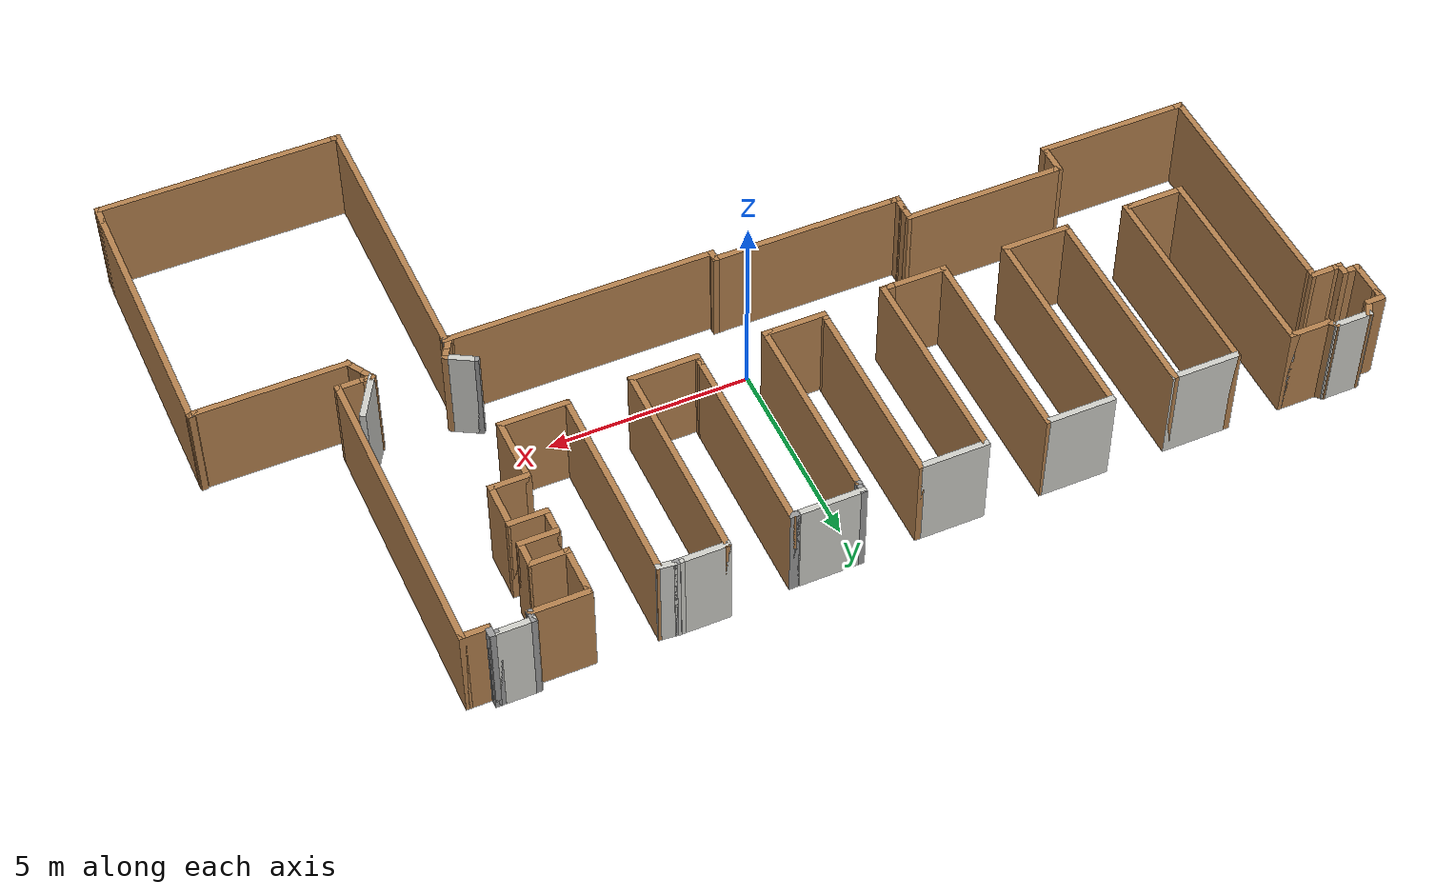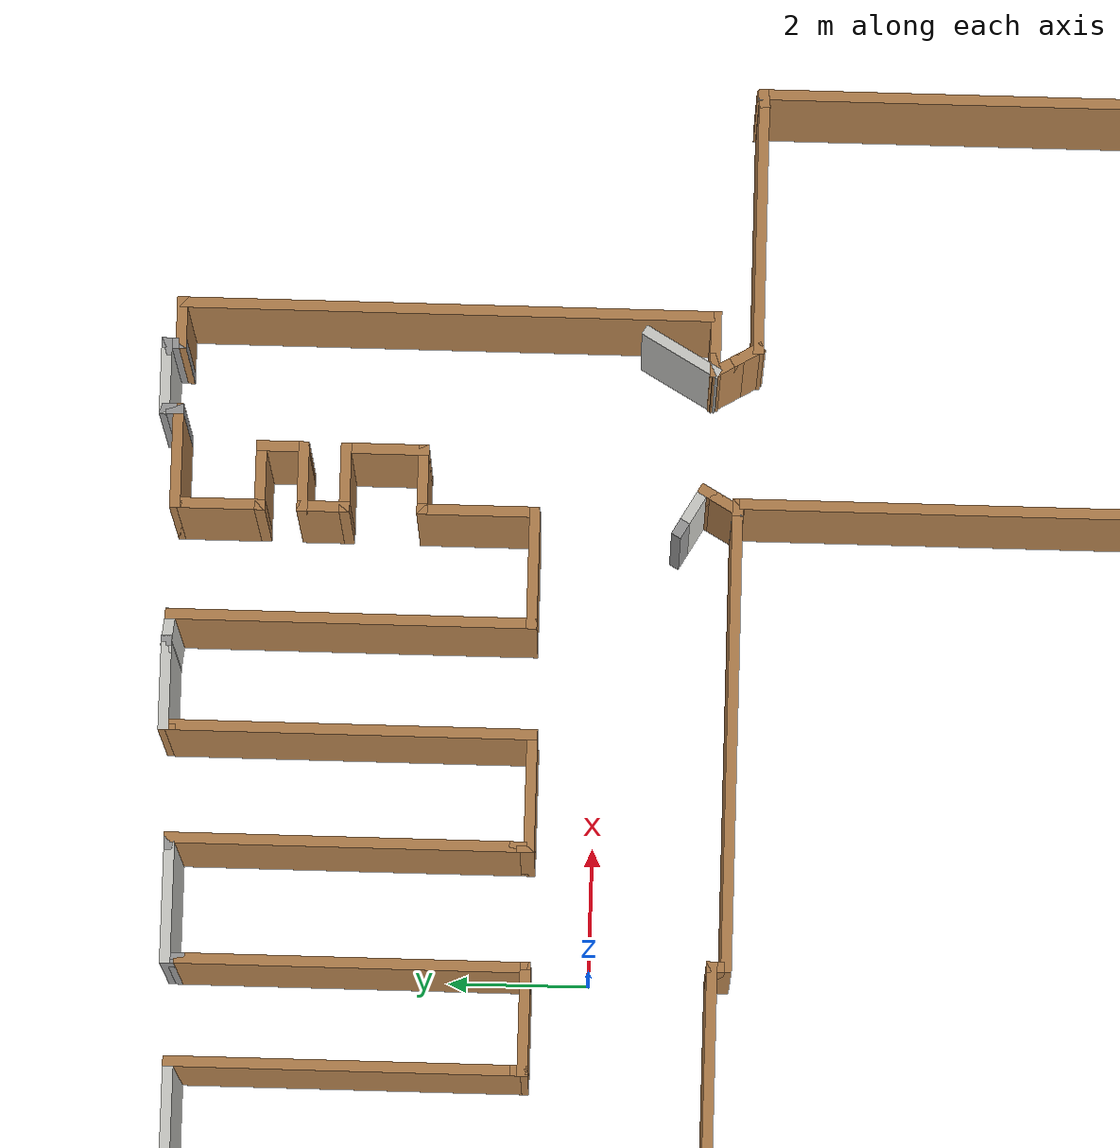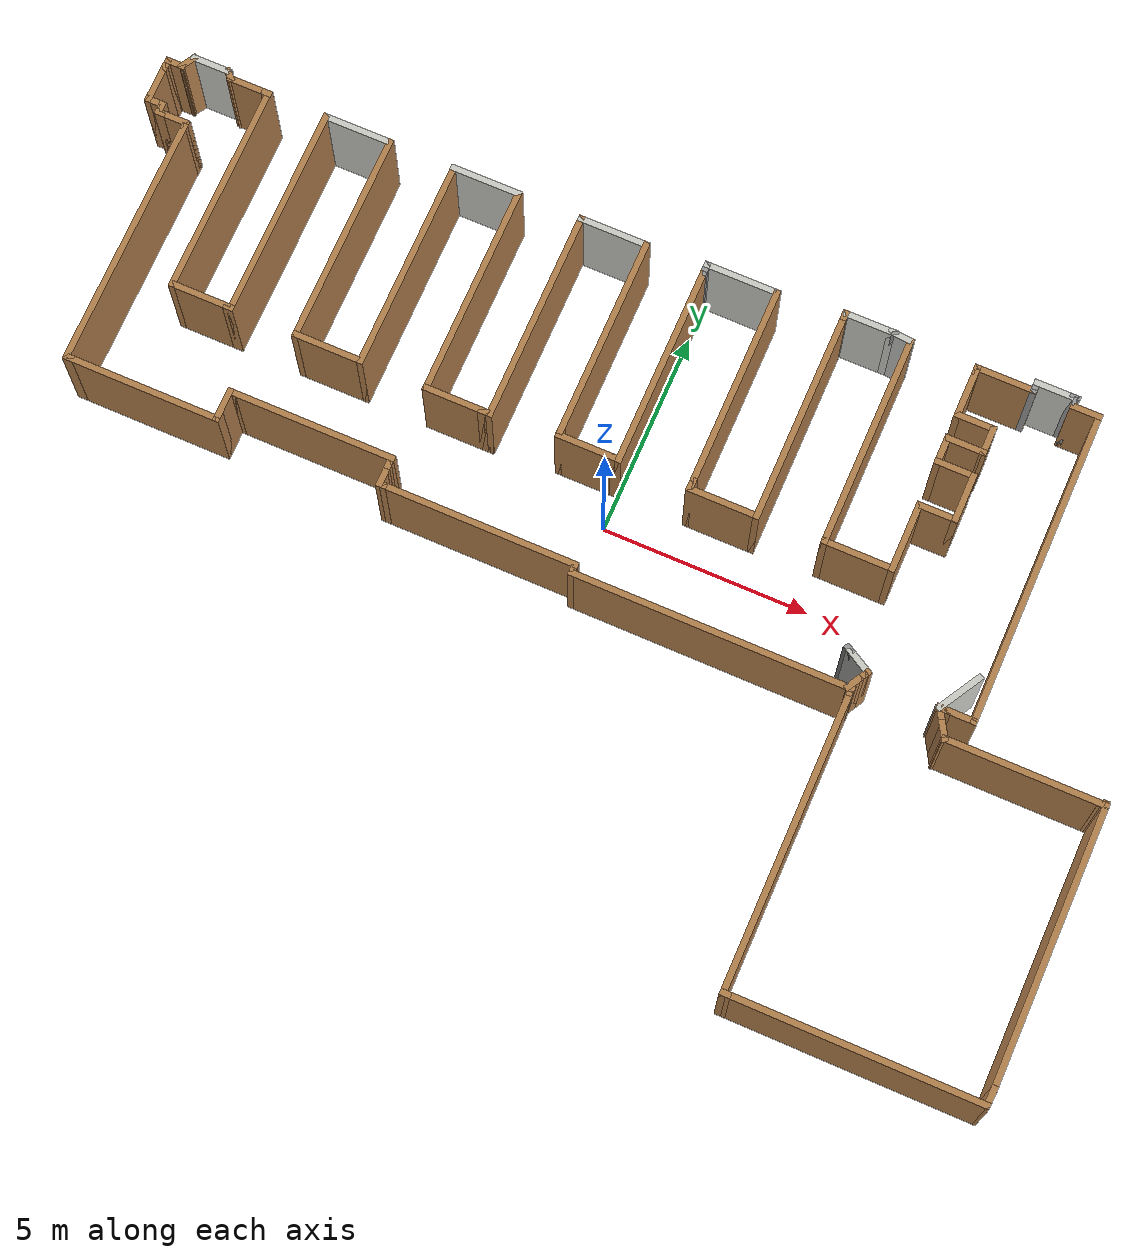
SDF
<?xml version='1.0'?>
<sdf version='1.6'>
  <model name='ecst_v3'>
    <pose frame=''>-0.363758 -1.44014 0 0 -0 0</pose>
    <link name='Wall_0'>
      <collision name='Wall_0_Collision'>
        <geometry>
          <box>
            <size>5.25 0.15 2.5</size>
          </box>
        </geometry>
        <pose frame=''>0 0 1.25 0 -0 0</pose>
      </collision>
      <visual name='Wall_0_Visual'>
        <pose frame=''>0 0 1.25 0 -0 0</pose>
        <geometry>
          <box>
            <size>5.25 0.15 2.5</size>
          </box>
        </geometry>
        <material>
          <script>
            <uri>file://media/materials/scripts/gazebo.material</uri>
            <name>Gazebo/Wood</name>
          </script>
          <ambient>1 1 1 1</ambient>
        </material>
        <meta>
          <layer>0</layer>
        </meta>
      </visual>
      <pose frame=''>5.21294 4.93605 0 0 -0 -1.5708</pose>
    </link>
    <link name='Wall_1'>
      <collision name='Wall_1_Collision'>
        <geometry>
          <box>
            <size>1.75 0.15 2.5</size>
          </box>
        </geometry>
        <pose frame=''>0 0 1.25 0 -0 0</pose>
      </collision>
      <visual name='Wall_1_Visual'>
        <pose frame=''>0 0 1.25 0 -0 0</pose>
        <geometry>
          <box>
            <size>1.75 0.15 2.5</size>
          </box>
        </geometry>
        <material>
          <script>
            <uri>file://media/materials/scripts/gazebo.material</uri>
            <name>Gazebo/Wood</name>
          </script>
          <ambient>1 1 1 1</ambient>
        </material>
        <meta>
          <layer>0</layer>
        </meta>
      </visual>
      <pose frame=''>6.01294 2.38605 0 0 -0 0</pose>
    </link>
    <link name='Wall_10'>
      <collision name='Wall_10_Collision'>
        <geometry>
          <box>
            <size>1.25 0.15 2.5</size>
          </box>
        </geometry>
        <pose frame=''>0 0 1.25 0 -0 0</pose>
      </collision>
      <visual name='Wall_10_Visual'>
        <pose frame=''>0 0 1.25 0 -0 0</pose>
        <geometry>
          <box>
            <size>1.25 0.15 2.5</size>
          </box>
        </geometry>
        <material>
          <script>
            <uri>file://media/materials/scripts/gazebo.material</uri>
            <name>Gazebo/Wood</name>
          </script>
          <ambient>1 1 1 1</ambient>
        </material>
        <meta>
          <layer>0</layer>
        </meta>
      </visual>
      <pose frame=''>6.81294 6.83605 0 0 -0 1.5708</pose>
    </link>
    <link name='Wall_100'>
      <collision name='Wall_100_Collision'>
        <geometry>
          <box>
            <size>5 0.15 2.5</size>
          </box>
        </geometry>
        <pose frame=''>0 0 1.25 0 -0 0</pose>
      </collision>
      <visual name='Wall_100_Visual'>
        <pose frame=''>0 0 1.25 0 -0 0</pose>
        <geometry>
          <box>
            <size>5 0.15 2.5</size>
          </box>
        </geometry>
        <material>
          <script>
            <uri>file://media/materials/scripts/gazebo.material</uri>
            <name>Gazebo/Wood</name>
          </script>
          <ambient>1 1 1 1</ambient>
        </material>
        <meta>
          <layer>0</layer>
        </meta>
      </visual>
      <pose frame=''>-1.12064 4.85351 0 0 -0 -1.5708</pose>
    </link>
    <link name='Wall_101'>
      <collision name='Wall_101_Collision'>
        <geometry>
          <box>
            <size>0.25 0.15 2.5</size>
          </box>
        </geometry>
        <pose frame=''>0 0 1.25 0 -0 0</pose>
      </collision>
      <visual name='Wall_101_Visual'>
        <pose frame=''>0 0 1.25 0 -0 0</pose>
        <geometry>
          <box>
            <size>0.25 0.15 2.5</size>
          </box>
        </geometry>
        <material>
          <script>
            <uri>file://media/materials/scripts/gazebo.material</uri>
            <name>Gazebo/Wood</name>
          </script>
          <ambient>1 1 1 1</ambient>
        </material>
        <meta>
          <layer>0</layer>
        </meta>
      </visual>
      <pose frame=''>-1.12064 2.37851 0 0 -0 -1.5708</pose>
    </link>
    <link name='Wall_102'>
      <collision name='Wall_102_Collision'>
        <geometry>
          <box>
            <size>1.5 0.15 2.5</size>
          </box>
        </geometry>
        <pose frame=''>0 0 1.25 0 -0 0</pose>
      </collision>
      <visual name='Wall_102_Visual'>
        <pose frame=''>0 0 1.25 0 -0 0</pose>
        <geometry>
          <box>
            <size>1.5 0.15 2.5</size>
          </box>
        </geometry>
        <material>
          <script>
            <uri>file://media/materials/scripts/gazebo.material</uri>
            <name>Gazebo/Wood</name>
          </script>
          <ambient>1 1 1 1</ambient>
        </material>
        <meta>
          <layer>0</layer>
        </meta>
      </visual>
      <pose frame=''>-0.445642 2.32851 0 0 -0 0</pose>
    </link>
    <link name='Wall_103'>
      <collision name='Wall_103_Collision'>
        <geometry>
          <box>
            <size>0.25 0.15 2.5</size>
          </box>
        </geometry>
        <pose frame=''>0 0 1.25 0 -0 0</pose>
      </collision>
      <visual name='Wall_103_Visual'>
        <pose frame=''>0 0 1.25 0 -0 0</pose>
        <geometry>
          <box>
            <size>0.25 0.15 2.5</size>
          </box>
        </geometry>
        <material>
          <script>
            <uri>file://media/materials/scripts/gazebo.material</uri>
            <name>Gazebo/Wood</name>
          </script>
          <ambient>1 1 1 1</ambient>
        </material>
        <meta>
          <layer>0</layer>
        </meta>
      </visual>
      <pose frame=''>0.279358 2.32851 0 0 -0 0</pose>
    </link>
    <link name='Wall_104'>
      <collision name='Wall_104_Collision'>
        <geometry>
          <box>
            <size>5 0.15 2.5</size>
          </box>
        </geometry>
        <pose frame=''>0 0 1.25 0 -0 0</pose>
      </collision>
      <visual name='Wall_104_Visual'>
        <pose frame=''>0 0 1.25 0 -0 0</pose>
        <geometry>
          <box>
            <size>5 0.15 2.5</size>
          </box>
        </geometry>
        <material>
          <script>
            <uri>file://media/materials/scripts/gazebo.material</uri>
            <name>Gazebo/Wood</name>
          </script>
          <ambient>1 1 1 1</ambient>
        </material>
        <meta>
          <layer>0</layer>
        </meta>
      </visual>
      <pose frame=''>0.329358 4.75351 0 0 -0 1.5708</pose>
    </link>
    <link name='Wall_105'>
      <collision name='Wall_105_Collision'>
        <geometry>
          <box>
            <size>0.25 0.15 2.5</size>
          </box>
        </geometry>
        <pose frame=''>0 0 1.25 0 -0 0</pose>
      </collision>
      <visual name='Wall_105_Visual'>
        <pose frame=''>0 0 1.25 0 -0 0</pose>
        <geometry>
          <box>
            <size>0.25 0.15 2.5</size>
          </box>
        </geometry>
        <material>
          <script>
            <uri>file://media/materials/scripts/gazebo.material</uri>
            <name>Gazebo/Grey</name>
          </script>
          <ambient>1 1 1 1</ambient>
        </material>
        <meta>
          <layer>0</layer>
        </meta>
      </visual>
      <pose frame=''>0.329358 7.22851 0 0 -0 1.5708</pose>
    </link>
    <link name='Wall_106'>
      <collision name='Wall_106_Collision'>
        <geometry>
          <box>
            <size>0.25 0.15 2.5</size>
          </box>
        </geometry>
        <pose frame=''>0 0 1.25 0 -0 0</pose>
      </collision>
      <visual name='Wall_106_Visual'>
        <pose frame=''>0 0 1.25 0 -0 0</pose>
        <geometry>
          <box>
            <size>0.25 0.15 2.5</size>
          </box>
        </geometry>
        <material>
          <script>
            <uri>file://media/materials/scripts/gazebo.material</uri>
            <name>Gazebo/Grey</name>
          </script>
          <ambient>1 1 1 1</ambient>
        </material>
        <meta>
          <layer>0</layer>
        </meta>
      </visual>
      <pose frame=''>0.329358 7.32851 0 0 -0 1.5708</pose>
    </link>
    <link name='Wall_107'>
      <collision name='Wall_107_Collision'>
        <geometry>
          <box>
            <size>1.75 0.15 2.5</size>
          </box>
        </geometry>
        <pose frame=''>0 0 1.25 0 -0 0</pose>
      </collision>
      <visual name='Wall_107_Visual'>
        <pose frame=''>0 0 1.25 0 -0 0</pose>
        <geometry>
          <box>
            <size>1.75 0.15 2.5</size>
          </box>
        </geometry>
        <material>
          <script>
            <uri>file://media/materials/scripts/gazebo.material</uri>
            <name>Gazebo/CeilingTiled</name>
          </script>
          <ambient>1 1 1 1</ambient>
        </material>
        <meta>
          <layer>0</layer>
        </meta>
      </visual>
      <pose frame=''>1.12936 7.37851 0 0 -0 0</pose>
    </link>
    <link name='Wall_108'>
      <collision name='Wall_108_Collision'>
        <geometry>
          <box>
            <size>0.15 0.15 2.5</size>
          </box>
        </geometry>
        <pose frame=''>0 0 1.25 0 -0 0</pose>
      </collision>
      <visual name='Wall_108_Visual'>
        <pose frame=''>0 0 1.25 0 -0 0</pose>
        <geometry>
          <box>
            <size>0.15 0.15 2.5</size>
          </box>
        </geometry>
        <material>
          <script>
            <uri>file://media/materials/scripts/gazebo.material</uri>
            <name>Gazebo/Grey</name>
          </script>
          <ambient>1 1 1 1</ambient>
        </material>
        <meta>
          <layer>0</layer>
        </meta>
      </visual>
      <pose frame=''>1.92936 7.37851 0 0 -0 0</pose>
    </link>
    <link name='Wall_109'>
      <collision name='Wall_109_Collision'>
        <geometry>
          <box>
            <size>0.25 0.15 2.5</size>
          </box>
        </geometry>
        <pose frame=''>0 0 1.25 0 -0 0</pose>
      </collision>
      <visual name='Wall_109_Visual'>
        <pose frame=''>0 0 1.25 0 -0 0</pose>
        <geometry>
          <box>
            <size>0.25 0.15 2.5</size>
          </box>
        </geometry>
        <material>
          <script>
            <uri>file://media/materials/scripts/gazebo.material</uri>
            <name>Gazebo/Grey</name>
          </script>
          <ambient>1 1 1 1</ambient>
        </material>
        <meta>
          <layer>0</layer>
        </meta>
      </visual>
      <pose frame=''>1.97936 7.37851 0 0 -0 0</pose>
    </link>
    <link name='Wall_11'>
      <collision name='Wall_11_Collision'>
        <geometry>
          <box>
            <size>0.25 0.15 2.5</size>
          </box>
        </geometry>
        <pose frame=''>0 0 1.25 0 -0 0</pose>
      </collision>
      <visual name='Wall_11_Visual'>
        <pose frame=''>0 0 1.25 0 -0 0</pose>
        <geometry>
          <box>
            <size>0.25 0.15 2.5</size>
          </box>
        </geometry>
        <material>
          <script>
            <uri>file://media/materials/scripts/gazebo.material</uri>
            <name>Gazebo/Wood</name>
          </script>
          <ambient>1 1 1 1</ambient>
        </material>
        <meta>
          <layer>0</layer>
        </meta>
      </visual>
      <pose frame=''>6.81294 7.43605 0 0 -0 1.5708</pose>
    </link>
    <link name='Wall_110'>
      <collision name='Wall_110_Collision'>
        <geometry>
          <box>
            <size>5 0.15 2.5</size>
          </box>
        </geometry>
        <pose frame=''>0 0 1.25 0 -0 0</pose>
      </collision>
      <visual name='Wall_110_Visual'>
        <pose frame=''>0 0 1.25 0 -0 0</pose>
        <geometry>
          <box>
            <size>5 0.15 2.5</size>
          </box>
        </geometry>
        <material>
          <script>
            <uri>file://media/materials/scripts/gazebo.material</uri>
            <name>Gazebo/Wood</name>
          </script>
          <ambient>1 1 1 1</ambient>
        </material>
        <meta>
          <layer>0</layer>
        </meta>
      </visual>
      <pose frame=''>2.02936 4.95351 0 0 -0 -1.5708</pose>
    </link>
    <link name='Wall_113'>
      <collision name='Wall_113_Collision'>
        <geometry>
          <box>
            <size>0.25 0.15 2.5</size>
          </box>
        </geometry>
        <pose frame=''>0 0 1.25 0 -0 0</pose>
      </collision>
      <visual name='Wall_113_Visual'>
        <pose frame=''>0 0 1.25 0 -0 0</pose>
        <geometry>
          <box>
            <size>0.25 0.15 2.5</size>
          </box>
        </geometry>
        <material>
          <script>
            <uri>file://media/materials/scripts/gazebo.material</uri>
            <name>Gazebo/Wood</name>
          </script>
          <ambient>1 1 1 1</ambient>
        </material>
        <meta>
          <layer>0</layer>
        </meta>
      </visual>
      <pose frame=''>2.02936 2.47851 0 0 -0 -1.5708</pose>
    </link>
    <link name='Wall_114'>
      <collision name='Wall_114_Collision'>
        <geometry>
          <box>
            <size>0.25 0.15 2.5</size>
          </box>
        </geometry>
        <pose frame=''>0 0 1.25 0 -0 0</pose>
      </collision>
      <visual name='Wall_114_Visual'>
        <pose frame=''>0 0 1.25 0 -0 0</pose>
        <geometry>
          <box>
            <size>0.25 0.15 2.5</size>
          </box>
        </geometry>
        <material>
          <script>
            <uri>file://media/materials/scripts/gazebo.material</uri>
            <name>Gazebo/Wood</name>
          </script>
          <ambient>1 1 1 1</ambient>
        </material>
        <meta>
          <layer>0</layer>
        </meta>
      </visual>
      <pose frame=''>2.02936 2.37851 0 0 -0 -1.5708</pose>
    </link>
    <link name='Wall_115'>
      <collision name='Wall_115_Collision'>
        <geometry>
          <box>
            <size>1.75 0.15 2.5</size>
          </box>
        </geometry>
        <pose frame=''>0 0 1.25 0 -0 0</pose>
      </collision>
      <visual name='Wall_115_Visual'>
        <pose frame=''>0 0 1.25 0 -0 0</pose>
        <geometry>
          <box>
            <size>1.75 0.15 2.5</size>
          </box>
        </geometry>
        <material>
          <script>
            <uri>file://media/materials/scripts/gazebo.material</uri>
            <name>Gazebo/Wood</name>
          </script>
          <ambient>1 1 1 1</ambient>
        </material>
        <meta>
          <layer>0</layer>
        </meta>
      </visual>
      <pose frame=''>2.82936 2.32851 0 0 -0 0</pose>
    </link>
    <link name='Wall_116'>
      <collision name='Wall_116_Collision'>
        <geometry>
          <box>
            <size>5.25 0.15 2.5</size>
          </box>
        </geometry>
        <pose frame=''>0 0 1.25 0 -0 0</pose>
      </collision>
      <visual name='Wall_116_Visual'>
        <pose frame=''>0 0 1.25 0 -0 0</pose>
        <geometry>
          <box>
            <size>5.25 0.15 2.5</size>
          </box>
        </geometry>
        <material>
          <script>
            <uri>file://media/materials/scripts/gazebo.material</uri>
            <name>Gazebo/Wood</name>
          </script>
          <ambient>1 1 1 1</ambient>
        </material>
        <meta>
          <layer>0</layer>
        </meta>
      </visual>
      <pose frame=''>3.62936 4.87851 0 0 -0 1.5708</pose>
    </link>
    <link name='Wall_117'>
      <collision name='Wall_117_Collision'>
        <geometry>
          <box>
            <size>0.25 0.15 2.5</size>
          </box>
        </geometry>
        <pose frame=''>0 0 1.25 0 -0 0</pose>
      </collision>
      <visual name='Wall_117_Visual'>
        <pose frame=''>0 0 1.25 0 -0 0</pose>
        <geometry>
          <box>
            <size>0.25 0.15 2.5</size>
          </box>
        </geometry>
        <material>
          <script>
            <uri>file://media/materials/scripts/gazebo.material</uri>
            <name>Gazebo/Wood</name>
          </script>
          <ambient>1 1 1 1</ambient>
        </material>
        <meta>
          <layer>0</layer>
        </meta>
      </visual>
      <pose frame=''>3.62936 7.47851 0 0 -0 1.5708</pose>
    </link>
    <link name='Wall_118'>
      <collision name='Wall_118_Collision'>
        <geometry>
          <box>
            <size>1.25 0.15 2.5</size>
          </box>
        </geometry>
        <pose frame=''>0 0 1.25 0 -0 0</pose>
      </collision>
      <visual name='Wall_118_Visual'>
        <pose frame=''>0 0 1.25 0 -0 0</pose>
        <geometry>
          <box>
            <size>1.25 0.15 2.5</size>
          </box>
        </geometry>
        <material>
          <script>
            <uri>file://media/materials/scripts/gazebo.material</uri>
            <name>Gazebo/CeilingTiled</name>
          </script>
          <ambient>1 1 1 1</ambient>
        </material>
        <meta>
          <layer>0</layer>
        </meta>
      </visual>
      <pose frame=''>4.17936 7.52851 0 0 -0 0</pose>
    </link>
    <link name='Wall_119'>
      <collision name='Wall_119_Collision'>
        <geometry>
          <box>
            <size>0.25 0.15 2.5</size>
          </box>
        </geometry>
        <pose frame=''>0 0 1.25 0 -0 0</pose>
      </collision>
      <visual name='Wall_119_Visual'>
        <pose frame=''>0 0 1.25 0 -0 0</pose>
        <geometry>
          <box>
            <size>0.25 0.15 2.5</size>
          </box>
        </geometry>
        <material>
          <script>
            <uri>file://media/materials/scripts/gazebo.material</uri>
            <name>Gazebo/CeilingTiled</name>
          </script>
          <ambient>1 1 1 1</ambient>
        </material>
        <meta>
          <layer>0</layer>
        </meta>
      </visual>
      <pose frame=''>4.77936 7.52851 0 0 -0 0</pose>
    </link>
    <link name='Wall_12'>
      <collision name='Wall_12_Collision'>
        <geometry>
          <box>
            <size>1.5 0.15 2.5</size>
          </box>
        </geometry>
        <pose frame=''>0 0 1.25 0 -0 0</pose>
      </collision>
      <visual name='Wall_12_Visual'>
        <pose frame=''>0 0 1.25 0 -0 0</pose>
        <geometry>
          <box>
            <size>1.5 0.15 2.5</size>
          </box>
        </geometry>
        <material>
          <script>
            <uri>file://media/materials/scripts/gazebo.material</uri>
            <name>Gazebo/Wood</name>
          </script>
          <ambient>1 1 1 1</ambient>
        </material>
        <meta>
          <layer>0</layer>
        </meta>
      </visual>
      <pose frame=''>7.48794 7.48605 0 0 -0 0</pose>
    </link>
    <link name='Wall_120'>
      <collision name='Wall_120_Collision'>
        <geometry>
          <box>
            <size>0.15 0.15 2.5</size>
          </box>
        </geometry>
        <pose frame=''>0 0 1.25 0 -0 0</pose>
      </collision>
      <visual name='Wall_120_Visual'>
        <pose frame=''>0 0 1.25 0 -0 0</pose>
        <geometry>
          <box>
            <size>0.15 0.15 2.5</size>
          </box>
        </geometry>
        <material>
          <script>
            <uri>file://media/materials/scripts/gazebo.material</uri>
            <name>Gazebo/Grey</name>
          </script>
          <ambient>1 1 1 1</ambient>
        </material>
        <meta>
          <layer>0</layer>
        </meta>
      </visual>
      <pose frame=''>4.82936 7.52851 0 0 -0 0</pose>
    </link>
    <link name='Wall_121'>
      <collision name='Wall_121_Collision'>
        <geometry>
          <box>
            <size>0.15 0.15 2.5</size>
          </box>
        </geometry>
        <pose frame=''>0 0 1.25 0 -0 0</pose>
      </collision>
      <visual name='Wall_121_Visual'>
        <pose frame=''>0 0 1.25 0 -0 0</pose>
        <geometry>
          <box>
            <size>0.15 0.15 2.5</size>
          </box>
        </geometry>
        <material>
          <script>
            <uri>file://media/materials/scripts/gazebo.material</uri>
            <name>Gazebo/CeilingTiled</name>
          </script>
          <ambient>1 1 1 1</ambient>
        </material>
        <meta>
          <layer>0</layer>
        </meta>
      </visual>
      <pose frame=''>4.82936 7.52851 0 0 -0 0</pose>
    </link>
    <link name='Wall_122'>
      <collision name='Wall_122_Collision'>
        <geometry>
          <box>
            <size>0.535922 0.15 2.5</size>
          </box>
        </geometry>
        <pose frame=''>0 0 1.25 0 -0 0</pose>
      </collision>
      <visual name='Wall_122_Visual'>
        <pose frame=''>0 0 1.25 0 -0 0</pose>
        <geometry>
          <box>
            <size>0.535922 0.15 2.5</size>
          </box>
        </geometry>
        <material>
          <script>
            <uri>file://media/materials/scripts/gazebo.material</uri>
            <name>Gazebo/CeilingTiled</name>
          </script>
          <ambient>1 1 1 1</ambient>
        </material>
        <meta>
          <layer>0</layer>
        </meta>
      </visual>
      <pose frame=''>5.02115 7.50728 0 0 -0 -0.110265</pose>
    </link>
    <link name='Wall_126'>
      <collision name='Wall_126_Collision'>
        <geometry>
          <box>
            <size>0.15 0.15 2.5</size>
          </box>
        </geometry>
        <pose frame=''>0 0 1.25 0 -0 0</pose>
      </collision>
      <visual name='Wall_126_Visual'>
        <pose frame=''>0 0 1.25 0 -0 0</pose>
        <geometry>
          <box>
            <size>0.15 0.15 2.5</size>
          </box>
        </geometry>
        <material>
          <script>
            <uri>file://media/materials/scripts/gazebo.material</uri>
            <name>Gazebo/Grey</name>
          </script>
          <ambient>1 1 1 1</ambient>
        </material>
        <meta>
          <layer>0</layer>
        </meta>
      </visual>
      <pose frame=''>7.01294 -0.483173 0 0 -0 0</pose>
    </link>
    <link name='Wall_127'>
      <collision name='Wall_127_Collision'>
        <geometry>
          <box>
            <size>0.15 0.15 2.5</size>
          </box>
        </geometry>
        <pose frame=''>0 0 1.25 0 -0 0</pose>
      </collision>
      <visual name='Wall_127_Visual'>
        <pose frame=''>0 0 1.25 0 -0 0</pose>
        <geometry>
          <box>
            <size>0.15 0.15 2.5</size>
          </box>
        </geometry>
        <material>
          <script>
            <uri>file://media/materials/scripts/gazebo.material</uri>
            <name>Gazebo/Grey</name>
          </script>
          <ambient>1 1 1 1</ambient>
        </material>
        <meta>
          <layer>0</layer>
        </meta>
      </visual>
      <pose frame=''>7.01294 -0.483173 0 0 -0 0</pose>
    </link>
    <link name='Wall_128'>
      <collision name='Wall_128_Collision'>
        <geometry>
          <box>
            <size>0.15 0.15 2.5</size>
          </box>
        </geometry>
        <pose frame=''>0 0 1.25 0 -0 0</pose>
      </collision>
      <visual name='Wall_128_Visual'>
        <pose frame=''>0 0 1.25 0 -0 0</pose>
        <geometry>
          <box>
            <size>0.15 0.15 2.5</size>
          </box>
        </geometry>
        <material>
          <script>
            <uri>file://media/materials/scripts/gazebo.material</uri>
            <name>Gazebo/Grey</name>
          </script>
          <ambient>1 1 1 1</ambient>
        </material>
        <meta>
          <layer>0</layer>
        </meta>
      </visual>
      <pose frame=''>7.01294 -0.483173 0 0 -0 0</pose>
    </link>
    <link name='Wall_129'>
      <collision name='Wall_129_Collision'>
        <geometry>
          <box>
            <size>0.25 0.15 2.5</size>
          </box>
        </geometry>
        <pose frame=''>0 0 1.25 0 -0 0</pose>
      </collision>
      <visual name='Wall_129_Visual'>
        <pose frame=''>0 0 1.25 0 -0 0</pose>
        <geometry>
          <box>
            <size>0.25 0.15 2.5</size>
          </box>
        </geometry>
        <material>
          <script>
            <uri>file://media/materials/scripts/gazebo.material</uri>
            <name>Gazebo/Wood</name>
          </script>
          <ambient>1 1 1 1</ambient>
        </material>
        <meta>
          <layer>0</layer>
        </meta>
      </visual>
      <pose frame=''>6.96294 -0.483173 0 0 -0 3.14159</pose>
    </link>
    <link name='Wall_13'>
      <collision name='Wall_13_Collision'>
        <geometry>
          <box>
            <size>0.25 0.15 2.5</size>
          </box>
        </geometry>
        <pose frame=''>0 0 1.25 0 -0 0</pose>
      </collision>
      <visual name='Wall_13_Visual'>
        <pose frame=''>0 0 1.25 0 -0 0</pose>
        <geometry>
          <box>
            <size>0.25 0.15 2.5</size>
          </box>
        </geometry>
        <material>
          <script>
            <uri>file://media/materials/scripts/gazebo.material</uri>
            <name>Gazebo/Grey</name>
          </script>
          <ambient>1 1 1 1</ambient>
        </material>
        <meta>
          <layer>0</layer>
        </meta>
      </visual>
      <pose frame=''>8.16294 7.53605 0 0 -0 1.5708</pose>
    </link>
    <link name='Wall_130'>
      <collision name='Wall_130_Collision'>
        <geometry>
          <box>
            <size>0.16 0.15 2.5</size>
          </box>
        </geometry>
        <pose frame=''>0 0 1.25 0 -0 0</pose>
      </collision>
      <visual name='Wall_130_Visual'>
        <pose frame=''>0 0 1.25 0 -0 0</pose>
        <geometry>
          <box>
            <size>0.16 0.15 2.5</size>
          </box>
        </geometry>
        <material>
          <script>
            <uri>file://media/materials/scripts/gazebo.material</uri>
            <name>Gazebo/Grey</name>
          </script>
          <ambient>1 1 1 1</ambient>
        </material>
        <meta>
          <layer>0</layer>
        </meta>
      </visual>
      <pose frame=''>6.91794 -0.483173 0 0 -0 0</pose>
    </link>
    <link name='Wall_131'>
      <collision name='Wall_131_Collision'>
        <geometry>
          <box>
            <size>0.5 0.15 2.5</size>
          </box>
        </geometry>
        <pose frame=''>0 0 1.25 0 -0 0</pose>
      </collision>
      <visual name='Wall_131_Visual'>
        <pose frame=''>0 0 1.25 0 -0 0</pose>
        <geometry>
          <box>
            <size>0.5 0.15 2.5</size>
          </box>
        </geometry>
        <material>
          <script>
            <uri>file://media/materials/scripts/gazebo.material</uri>
            <name>Gazebo/Wood</name>
          </script>
          <ambient>1 1 1 1</ambient>
        </material>
        <meta>
          <layer>0</layer>
        </meta>
      </visual>
      <pose frame=''>7.01044 -0.331619 0 0 -0 1.0472</pose>
    </link>
    <link name='Wall_132'>
      <collision name='Wall_132_Collision'>
        <geometry>
          <box>
            <size>0.25 0.15 2.5</size>
          </box>
        </geometry>
        <pose frame=''>0 0 1.25 0 -0 0</pose>
      </collision>
      <visual name='Wall_132_Visual'>
        <pose frame=''>0 0 1.25 0 -0 0</pose>
        <geometry>
          <box>
            <size>0.25 0.15 2.5</size>
          </box>
        </geometry>
        <material>
          <script>
            <uri>file://media/materials/scripts/gazebo.material</uri>
            <name>Gazebo/Wood</name>
          </script>
          <ambient>1 1 1 1</ambient>
        </material>
        <meta>
          <layer>0</layer>
        </meta>
      </visual>
      <pose frame=''>7.12294 -0.136763 0 0 -0 1.0472</pose>
    </link>
    <link name='Wall_133'>
      <collision name='Wall_133_Collision'>
        <geometry>
          <box>
            <size>0.25 0.15 2.5</size>
          </box>
        </geometry>
        <pose frame=''>0 0 1.25 0 -0 0</pose>
      </collision>
      <visual name='Wall_133_Visual'>
        <pose frame=''>0 0 1.25 0 -0 0</pose>
        <geometry>
          <box>
            <size>0.25 0.15 2.5</size>
          </box>
        </geometry>
        <material>
          <script>
            <uri>file://media/materials/scripts/gazebo.material</uri>
            <name>Gazebo/Wood</name>
          </script>
          <ambient>1 1 1 1</ambient>
        </material>
        <meta>
          <layer>0</layer>
        </meta>
      </visual>
      <pose frame=''>7.17294 -0.050161 0 0 -0 1.0472</pose>
    </link>
    <link name='Wall_134'>
      <collision name='Wall_134_Collision'>
        <geometry>
          <box>
            <size>0.75 0.15 2.5</size>
          </box>
        </geometry>
        <pose frame=''>0 0 1.25 0 -0 0</pose>
      </collision>
      <visual name='Wall_134_Visual'>
        <pose frame=''>0 0 1.25 0 -0 0</pose>
        <geometry>
          <box>
            <size>0.75 0.15 2.5</size>
          </box>
        </geometry>
        <material>
          <script>
            <uri>file://media/materials/scripts/gazebo.material</uri>
            <name>Gazebo/CeilingTiled</name>
          </script>
          <ambient>1 1 1 1</ambient>
        </material>
        <meta>
          <layer>0</layer>
        </meta>
      </visual>
      <pose frame=''>6.93813 0.14314 0 0 -0 2.61799</pose>
    </link>
    <link name='Wall_135'>
      <collision name='Wall_135_Collision'>
        <geometry>
          <box>
            <size>0.25 0.15 2.5</size>
          </box>
        </geometry>
        <pose frame=''>0 0 1.25 0 -0 0</pose>
      </collision>
      <visual name='Wall_135_Visual'>
        <pose frame=''>0 0 1.25 0 -0 0</pose>
        <geometry>
          <box>
            <size>0.25 0.15 2.5</size>
          </box>
        </geometry>
        <material>
          <script>
            <uri>file://media/materials/scripts/gazebo.material</uri>
            <name>Gazebo/Grey</name>
          </script>
          <ambient>1 1 1 1</ambient>
        </material>
        <meta>
          <layer>0</layer>
        </meta>
      </visual>
      <pose frame=''>6.63502 0.318141 0 0 -0 2.61799</pose>
    </link>
    <link name='Wall_14'>
      <collision name='Wall_14_Collision'>
        <geometry>
          <box>
            <size>0.25 0.15 2.5</size>
          </box>
        </geometry>
        <pose frame=''>0 0 1.25 0 -0 0</pose>
      </collision>
      <visual name='Wall_14_Visual'>
        <pose frame=''>0 0 1.25 0 -0 0</pose>
        <geometry>
          <box>
            <size>0.25 0.15 2.5</size>
          </box>
        </geometry>
        <material>
          <script>
            <uri>file://media/materials/scripts/gazebo.material</uri>
            <name>Gazebo/Grey</name>
          </script>
          <ambient>1 1 1 1</ambient>
        </material>
        <meta>
          <layer>0</layer>
        </meta>
      </visual>
      <pose frame=''>8.16294 7.63605 0 0 -0 1.5708</pose>
    </link>
    <link name='Wall_15'>
      <collision name='Wall_15_Collision'>
        <geometry>
          <box>
            <size>1 0.15 2.5</size>
          </box>
        </geometry>
        <pose frame=''>0 0 1.25 0 -0 0</pose>
      </collision>
      <visual name='Wall_15_Visual'>
        <pose frame=''>0 0 1.25 0 -0 0</pose>
        <geometry>
          <box>
            <size>1 0.15 2.5</size>
          </box>
        </geometry>
        <material>
          <script>
            <uri>file://media/materials/scripts/gazebo.material</uri>
            <name>Gazebo/CeilingTiled</name>
          </script>
          <ambient>1 1 1 1</ambient>
        </material>
        <meta>
          <layer>0</layer>
        </meta>
      </visual>
      <pose frame=''>8.58794 7.68605 0 0 -0 0</pose>
    </link>
    <link name='Wall_16'>
      <collision name='Wall_16_Collision'>
        <geometry>
          <box>
            <size>0.25 0.15 2.5</size>
          </box>
        </geometry>
        <pose frame=''>0 0 1.25 0 -0 0</pose>
      </collision>
      <visual name='Wall_16_Visual'>
        <pose frame=''>0 0 1.25 0 -0 0</pose>
        <geometry>
          <box>
            <size>0.25 0.15 2.5</size>
          </box>
        </geometry>
        <material>
          <script>
            <uri>file://media/materials/scripts/gazebo.material</uri>
            <name>Gazebo/Grey</name>
          </script>
          <ambient>1 1 1 1</ambient>
        </material>
        <meta>
          <layer>0</layer>
        </meta>
      </visual>
      <pose frame=''>9.06294 7.68605 0 0 -0 0</pose>
    </link>
    <link name='Wall_17'>
      <collision name='Wall_17_Collision'>
        <geometry>
          <box>
            <size>0.25 0.15 2.5</size>
          </box>
        </geometry>
        <pose frame=''>0 0 1.25 0 -0 0</pose>
      </collision>
      <visual name='Wall_17_Visual'>
        <pose frame=''>0 0 1.25 0 -0 0</pose>
        <geometry>
          <box>
            <size>0.25 0.15 2.5</size>
          </box>
        </geometry>
        <material>
          <script>
            <uri>file://media/materials/scripts/gazebo.material</uri>
            <name>Gazebo/Grey</name>
          </script>
          <ambient>1 1 1 1</ambient>
        </material>
        <meta>
          <layer>0</layer>
        </meta>
      </visual>
      <pose frame=''>9.11294 7.63605 0 0 -0 -1.5708</pose>
    </link>
    <link name='Wall_18'>
      <collision name='Wall_18_Collision'>
        <geometry>
          <box>
            <size>0.25 0.15 2.5</size>
          </box>
        </geometry>
        <pose frame=''>0 0 1.25 0 -0 0</pose>
      </collision>
      <visual name='Wall_18_Visual'>
        <pose frame=''>0 0 1.25 0 -0 0</pose>
        <geometry>
          <box>
            <size>0.25 0.15 2.5</size>
          </box>
        </geometry>
        <material>
          <script>
            <uri>file://media/materials/scripts/gazebo.material</uri>
            <name>Gazebo/Grey</name>
          </script>
          <ambient>1 1 1 1</ambient>
        </material>
        <meta>
          <layer>0</layer>
        </meta>
      </visual>
      <pose frame=''>9.11294 7.53605 0 0 -0 -1.5708</pose>
    </link>
    <link name='Wall_19'>
      <collision name='Wall_19_Collision'>
        <geometry>
          <box>
            <size>0.75 0.15 2.5</size>
          </box>
        </geometry>
        <pose frame=''>0 0 1.25 0 -0 0</pose>
      </collision>
      <visual name='Wall_19_Visual'>
        <pose frame=''>0 0 1.25 0 -0 0</pose>
        <geometry>
          <box>
            <size>0.75 0.15 2.5</size>
          </box>
        </geometry>
        <material>
          <script>
            <uri>file://media/materials/scripts/gazebo.material</uri>
            <name>Gazebo/Wood</name>
          </script>
          <ambient>1 1 1 1</ambient>
        </material>
        <meta>
          <layer>0</layer>
        </meta>
      </visual>
      <pose frame=''>9.41294 7.48605 0 0 -0 0</pose>
    </link>
    <link name='Wall_2'>
      <collision name='Wall_2_Collision'>
        <geometry>
          <box>
            <size>1.75 0.15 2.5</size>
          </box>
        </geometry>
        <pose frame=''>0 0 1.25 0 -0 0</pose>
      </collision>
      <visual name='Wall_2_Visual'>
        <pose frame=''>0 0 1.25 0 -0 0</pose>
        <geometry>
          <box>
            <size>1.75 0.15 2.5</size>
          </box>
        </geometry>
        <material>
          <script>
            <uri>file://media/materials/scripts/gazebo.material</uri>
            <name>Gazebo/Wood</name>
          </script>
          <ambient>1 1 1 1</ambient>
        </material>
        <meta>
          <layer>0</layer>
        </meta>
      </visual>
      <pose frame=''>6.81294 3.18605 0 0 -0 1.5708</pose>
    </link>
    <link name='Wall_20'>
      <collision name='Wall_20_Collision'>
        <geometry>
          <box>
            <size>7.75 0.15 2.5</size>
          </box>
        </geometry>
        <pose frame=''>0 0 1.25 0 -0 0</pose>
      </collision>
      <visual name='Wall_20_Visual'>
        <pose frame=''>0 0 1.25 0 -0 0</pose>
        <geometry>
          <box>
            <size>7.75 0.15 2.5</size>
          </box>
        </geometry>
        <material>
          <script>
            <uri>file://media/materials/scripts/gazebo.material</uri>
            <name>Gazebo/Wood</name>
          </script>
          <ambient>1 1 1 1</ambient>
        </material>
        <meta>
          <layer>0</layer>
        </meta>
      </visual>
      <pose frame=''>9.71294 3.68605 0 0 -0 -1.5708</pose>
    </link>
    <link name='Wall_21'>
      <collision name='Wall_21_Collision'>
        <geometry>
          <box>
            <size>0.75 0.15 2.5</size>
          </box>
        </geometry>
        <pose frame=''>0 0 1.25 0 -0 0</pose>
      </collision>
      <visual name='Wall_21_Visual'>
        <pose frame=''>0 0 1.25 0 -0 0</pose>
        <geometry>
          <box>
            <size>0.75 0.15 2.5</size>
          </box>
        </geometry>
        <material>
          <script>
            <uri>file://media/materials/scripts/gazebo.material</uri>
            <name>Gazebo/Wood</name>
          </script>
          <ambient>1 1 1 1</ambient>
        </material>
        <meta>
          <layer>0</layer>
        </meta>
      </visual>
      <pose frame=''>9.41294 -0.113953 0 0 -0 3.14159</pose>
    </link>
    <link name='Wall_22'>
      <collision name='Wall_22_Collision'>
        <geometry>
          <box>
            <size>0.25 0.15 2.5</size>
          </box>
        </geometry>
        <pose frame=''>0 0 1.25 0 -0 0</pose>
      </collision>
      <visual name='Wall_22_Visual'>
        <pose frame=''>0 0 1.25 0 -0 0</pose>
        <geometry>
          <box>
            <size>0.25 0.15 2.5</size>
          </box>
        </geometry>
        <material>
          <script>
            <uri>file://media/materials/scripts/gazebo.material</uri>
            <name>Gazebo/Wood</name>
          </script>
          <ambient>1 1 1 1</ambient>
        </material>
        <meta>
          <layer>0</layer>
        </meta>
      </visual>
      <pose frame=''>9.06294 -0.113953 0 0 -0 3.14159</pose>
    </link>
    <link name='Wall_23'>
      <collision name='Wall_23_Collision'>
        <geometry>
          <box>
            <size>0.25 0.15 2.5</size>
          </box>
        </geometry>
        <pose frame=''>0 0 1.25 0 -0 0</pose>
      </collision>
      <visual name='Wall_23_Visual'>
        <pose frame=''>0 0 1.25 0 -0 0</pose>
        <geometry>
          <box>
            <size>0.25 0.15 2.5</size>
          </box>
        </geometry>
        <material>
          <script>
            <uri>file://media/materials/scripts/gazebo.material</uri>
            <name>Gazebo/Wood</name>
          </script>
          <ambient>1 1 1 1</ambient>
        </material>
        <meta>
          <layer>0</layer>
        </meta>
      </visual>
      <pose frame=''>8.96294 -0.113953 0 0 -0 3.14159</pose>
    </link>
    <link name='Wall_24'>
      <collision name='Wall_24_Collision'>
        <geometry>
          <box>
            <size>1.25 0.15 2.5</size>
          </box>
        </geometry>
        <pose frame=''>0 0 1.25 0 -0 0</pose>
      </collision>
      <visual name='Wall_24_Visual'>
        <pose frame=''>0 0 1.25 0 -0 0</pose>
        <geometry>
          <box>
            <size>1.25 0.15 2.5</size>
          </box>
        </geometry>
        <material>
          <script>
            <uri>file://media/materials/scripts/gazebo.material</uri>
            <name>Gazebo/CeilingTiled</name>
          </script>
          <ambient>1 1 1 1</ambient>
        </material>
        <meta>
          <layer>0</layer>
        </meta>
      </visual>
      <pose frame=''>9.18794 0.36236 0 0 -0 1.0472</pose>
    </link>
    <link name='Wall_26'>
      <collision name='Wall_26_Collision'>
        <geometry>
          <box>
            <size>0.5 0.15 2.5</size>
          </box>
        </geometry>
        <pose frame=''>0 0 1.25 0 -0 0</pose>
      </collision>
      <visual name='Wall_26_Visual'>
        <pose frame=''>0 0 1.25 0 -0 0</pose>
        <geometry>
          <box>
            <size>0.5 0.15 2.5</size>
          </box>
        </geometry>
        <material>
          <script>
            <uri>file://media/materials/scripts/gazebo.material</uri>
            <name>Gazebo/Wood</name>
          </script>
          <ambient>1 1 1 1</ambient>
        </material>
        <meta>
          <layer>0</layer>
        </meta>
      </visual>
      <pose frame=''>9.00044 -0.265508 0 0 -0 -1.0472</pose>
    </link>
    <link name='Wall_27'>
      <collision name='Wall_27_Collision'>
        <geometry>
          <box>
            <size>0.5 0.15 2.5</size>
          </box>
        </geometry>
        <pose frame=''>0 0 1.25 0 -0 0</pose>
      </collision>
      <visual name='Wall_27_Visual'>
        <pose frame=''>0 0 1.25 0 -0 0</pose>
        <geometry>
          <box>
            <size>0.5 0.15 2.5</size>
          </box>
        </geometry>
        <material>
          <script>
            <uri>file://media/materials/scripts/gazebo.material</uri>
            <name>Gazebo/Wood</name>
          </script>
          <ambient>1 1 1 1</ambient>
        </material>
        <meta>
          <layer>0</layer>
        </meta>
      </visual>
      <pose frame=''>9.17544 -0.568617 0 0 -0 -1.0472</pose>
    </link>
    <link name='Wall_28'>
      <collision name='Wall_28_Collision'>
        <geometry>
          <box>
            <size>3.75 0.15 2.5</size>
          </box>
        </geometry>
        <pose frame=''>0 0 1.25 0 -0 0</pose>
      </collision>
      <visual name='Wall_28_Visual'>
        <pose frame=''>0 0 1.25 0 -0 0</pose>
        <geometry>
          <box>
            <size>3.75 0.15 2.5</size>
          </box>
        </geometry>
        <material>
          <script>
            <uri>file://media/materials/scripts/gazebo.material</uri>
            <name>Gazebo/Wood</name>
          </script>
          <ambient>1 1 1 1</ambient>
        </material>
        <meta>
          <layer>0</layer>
        </meta>
      </visual>
      <pose frame=''>11.0629 -0.720171 0 0 -0 0</pose>
    </link>
    <link name='Wall_29'>
      <collision name='Wall_29_Collision'>
        <geometry>
          <box>
            <size>0.15 0.15 2.5</size>
          </box>
        </geometry>
        <pose frame=''>0 0 1.25 0 -0 0</pose>
      </collision>
      <visual name='Wall_29_Visual'>
        <pose frame=''>0 0 1.25 0 -0 0</pose>
        <geometry>
          <box>
            <size>0.15 0.15 2.5</size>
          </box>
        </geometry>
        <material>
          <script>
            <uri>file://media/materials/scripts/gazebo.material</uri>
            <name>Gazebo/Wood</name>
          </script>
          <ambient>1 1 1 1</ambient>
        </material>
        <meta>
          <layer>0</layer>
        </meta>
      </visual>
      <pose frame=''>12.8629 -0.720171 0 0 -0 0</pose>
    </link>
    <link name='Wall_3'>
      <collision name='Wall_3_Collision'>
        <geometry>
          <box>
            <size>1 0.15 2.5</size>
          </box>
        </geometry>
        <pose frame=''>0 0 1.25 0 -0 0</pose>
      </collision>
      <visual name='Wall_3_Visual'>
        <pose frame=''>0 0 1.25 0 -0 0</pose>
        <geometry>
          <box>
            <size>1 0.15 2.5</size>
          </box>
        </geometry>
        <material>
          <script>
            <uri>file://media/materials/scripts/gazebo.material</uri>
            <name>Gazebo/Wood</name>
          </script>
          <ambient>1 1 1 1</ambient>
        </material>
        <meta>
          <layer>0</layer>
        </meta>
      </visual>
      <pose frame=''>7.23794 3.98605 0 0 -0 0</pose>
    </link>
    <link name='Wall_30'>
      <collision name='Wall_30_Collision'>
        <geometry>
          <box>
            <size>0.266016 0.15 2.5</size>
          </box>
        </geometry>
        <pose frame=''>0 0 1.25 0 -0 0</pose>
      </collision>
      <visual name='Wall_30_Visual'>
        <pose frame=''>0 0 1.25 0 -0 0</pose>
        <geometry>
          <box>
            <size>0.266016 0.15 2.5</size>
          </box>
        </geometry>
        <material>
          <script>
            <uri>file://media/materials/scripts/gazebo.material</uri>
            <name>Gazebo/Wood</name>
          </script>
          <ambient>1 1 1 1</ambient>
        </material>
        <meta>
          <layer>0</layer>
        </meta>
      </visual>
      <pose frame=''>12.9205 -0.712652 0 0 -0 0.129981</pose>
    </link>
    <link name='Wall_31'>
      <collision name='Wall_31_Collision'>
        <geometry>
          <box>
            <size>6.72196 0.15 2.5</size>
          </box>
        </geometry>
        <pose frame=''>0 0 1.25 0 -0 0</pose>
      </collision>
      <visual name='Wall_31_Visual'>
        <pose frame=''>0 0 1.25 0 -0 0</pose>
        <geometry>
          <box>
            <size>6.72196 0.15 2.5</size>
          </box>
        </geometry>
        <material>
          <script>
            <uri>file://media/materials/scripts/gazebo.material</uri>
            <name>Gazebo/Wood</name>
          </script>
          <ambient>1 1 1 1</ambient>
        </material>
        <meta>
          <layer>0</layer>
        </meta>
      </visual>
      <pose frame=''>12.978 -4.00615 0 0 -0 -1.5708</pose>
    </link>
    <link name='Wall_32'>
      <collision name='Wall_32_Collision'>
        <geometry>
          <box>
            <size>0.534835 0.15 2.5</size>
          </box>
        </geometry>
        <pose frame=''>0 0 1.25 0 -0 0</pose>
      </collision>
      <visual name='Wall_32_Visual'>
        <pose frame=''>0 0 1.25 0 -0 0</pose>
        <geometry>
          <box>
            <size>0.534835 0.15 2.5</size>
          </box>
        </geometry>
        <material>
          <script>
            <uri>file://media/materials/scripts/gazebo.material</uri>
            <name>Gazebo/Wood</name>
          </script>
          <ambient>1 1 1 1</ambient>
        </material>
        <meta>
          <layer>0</layer>
        </meta>
      </visual>
      <pose frame=''>12.9705 -7.4909 0 0 -0 -1.60988</pose>
    </link>
    <link name='Wall_38'>
      <collision name='Wall_38_Collision'>
        <geometry>
          <box>
            <size>0.15 0.15 2.5</size>
          </box>
        </geometry>
        <pose frame=''>0 0 1.25 0 -0 0</pose>
      </collision>
      <visual name='Wall_38_Visual'>
        <pose frame=''>0 0 1.25 0 -0 0</pose>
        <geometry>
          <box>
            <size>0.15 0.15 2.5</size>
          </box>
        </geometry>
        <material>
          <script>
            <uri>file://media/materials/scripts/gazebo.material</uri>
            <name>Gazebo/Wood</name>
          </script>
          <ambient>1 1 1 1</ambient>
        </material>
        <meta>
          <layer>0</layer>
        </meta>
      </visual>
      <pose frame=''>12.9527 -0.687517 0 0 -0 0</pose>
    </link>
    <link name='Wall_4'>
      <collision name='Wall_4_Collision'>
        <geometry>
          <box>
            <size>1.25 0.15 2.5</size>
          </box>
        </geometry>
        <pose frame=''>0 0 1.25 0 -0 0</pose>
      </collision>
      <visual name='Wall_4_Visual'>
        <pose frame=''>0 0 1.25 0 -0 0</pose>
        <geometry>
          <box>
            <size>1.25 0.15 2.5</size>
          </box>
        </geometry>
        <material>
          <script>
            <uri>file://media/materials/scripts/gazebo.material</uri>
            <name>Gazebo/Wood</name>
          </script>
          <ambient>1 1 1 1</ambient>
        </material>
        <meta>
          <layer>0</layer>
        </meta>
      </visual>
      <pose frame=''>7.66294 4.53605 0 0 -0 1.5708</pose>
    </link>
    <link name='Wall_42'>
      <collision name='Wall_42_Collision'>
        <geometry>
          <box>
            <size>0.15 0.15 2.5</size>
          </box>
        </geometry>
        <pose frame=''>0 0 1.25 0 -0 0</pose>
      </collision>
      <visual name='Wall_42_Visual'>
        <pose frame=''>0 0 1.25 0 -0 0</pose>
        <geometry>
          <box>
            <size>0.15 0.15 2.5</size>
          </box>
        </geometry>
        <material>
          <script>
            <uri>file://media/materials/scripts/gazebo.material</uri>
            <name>Gazebo/Grey</name>
          </script>
          <ambient>0 0 0 1</ambient>
        </material>
        <meta>
          <layer>0</layer>
        </meta>
      </visual>
      <pose frame=''>12.9678 -0.702555 0 0 -0 0</pose>
    </link>
    <link name='Wall_45'>
      <collision name='Wall_45_Collision'>
        <geometry>
          <box>
            <size>6 0.15 2.5</size>
          </box>
        </geometry>
        <pose frame=''>0 0 1.25 0 -0 0</pose>
      </collision>
      <visual name='Wall_45_Visual'>
        <pose frame=''>0 0 1.25 0 -0 0</pose>
        <geometry>
          <box>
            <size>6 0.15 2.5</size>
          </box>
        </geometry>
        <material>
          <script>
            <uri>file://media/materials/scripts/gazebo.material</uri>
            <name>Gazebo/Wood</name>
          </script>
          <ambient>1 1 1 1</ambient>
        </material>
        <meta>
          <layer>0</layer>
        </meta>
      </visual>
      <pose frame=''>10.0379 -7.68317 0 0 -0 3.14159</pose>
    </link>
    <link name='Wall_46'>
      <collision name='Wall_46_Collision'>
        <geometry>
          <box>
            <size>0.25 0.15 2.5</size>
          </box>
        </geometry>
        <pose frame=''>0 0 1.25 0 -0 0</pose>
      </collision>
      <visual name='Wall_46_Visual'>
        <pose frame=''>0 0 1.25 0 -0 0</pose>
        <geometry>
          <box>
            <size>0.25 0.15 2.5</size>
          </box>
        </geometry>
        <material>
          <script>
            <uri>file://media/materials/scripts/gazebo.material</uri>
            <name>Gazebo/Wood</name>
          </script>
          <ambient>1 1 1 1</ambient>
        </material>
        <meta>
          <layer>0</layer>
        </meta>
      </visual>
      <pose frame=''>7.06294 -7.68317 0 0 -0 3.14159</pose>
    </link>
    <link name='Wall_47'>
      <collision name='Wall_47_Collision'>
        <geometry>
          <box>
            <size>7.25 0.15 2.5</size>
          </box>
        </geometry>
        <pose frame=''>0 0 1.25 0 -0 0</pose>
      </collision>
      <visual name='Wall_47_Visual'>
        <pose frame=''>0 0 1.25 0 -0 0</pose>
        <geometry>
          <box>
            <size>7.25 0.15 2.5</size>
          </box>
        </geometry>
        <material>
          <script>
            <uri>file://media/materials/scripts/gazebo.material</uri>
            <name>Gazebo/Wood</name>
          </script>
          <ambient>1 1 1 1</ambient>
        </material>
        <meta>
          <layer>0</layer>
        </meta>
      </visual>
      <pose frame=''>7.01294 -4.13317 0 0 -0 1.5708</pose>
    </link>
    <link name='Wall_48'>
      <collision name='Wall_48_Collision'>
        <geometry>
          <box>
            <size>0.25 0.15 2.5</size>
          </box>
        </geometry>
        <pose frame=''>0 0 1.25 0 -0 0</pose>
      </collision>
      <visual name='Wall_48_Visual'>
        <pose frame=''>0 0 1.25 0 -0 0</pose>
        <geometry>
          <box>
            <size>0.25 0.15 2.5</size>
          </box>
        </geometry>
        <material>
          <script>
            <uri>file://media/materials/scripts/gazebo.material</uri>
            <name>Gazebo/Wood</name>
          </script>
          <ambient>1 1 1 1</ambient>
        </material>
        <meta>
          <layer>0</layer>
        </meta>
      </visual>
      <pose frame=''>7.01294 -0.533174 0 0 -0 1.5708</pose>
    </link>
    <link name='Wall_49'>
      <collision name='Wall_49_Collision'>
        <geometry>
          <box>
            <size>6.75 0.15 2.5</size>
          </box>
        </geometry>
        <pose frame=''>0 0 1.25 0 -0 0</pose>
      </collision>
      <visual name='Wall_49_Visual'>
        <pose frame=''>0 0 1.25 0 -0 0</pose>
        <geometry>
          <box>
            <size>6.75 0.15 2.5</size>
          </box>
        </geometry>
        <material>
          <script>
            <uri>file://media/materials/scripts/gazebo.material</uri>
            <name>Gazebo/Wood</name>
          </script>
          <ambient>1 1 1 1</ambient>
        </material>
        <meta>
          <layer>0</layer>
        </meta>
      </visual>
      <pose frame=''>3.71294 -0.483173 0 0 -0 3.14159</pose>
    </link>
    <link name='Wall_5'>
      <collision name='Wall_5_Collision'>
        <geometry>
          <box>
            <size>1 0.15 2.5</size>
          </box>
        </geometry>
        <pose frame=''>0 0 1.25 0 -0 0</pose>
      </collision>
      <visual name='Wall_5_Visual'>
        <pose frame=''>0 0 1.25 0 -0 0</pose>
        <geometry>
          <box>
            <size>1 0.15 2.5</size>
          </box>
        </geometry>
        <material>
          <script>
            <uri>file://media/materials/scripts/gazebo.material</uri>
            <name>Gazebo/Wood</name>
          </script>
          <ambient>1 1 1 1</ambient>
        </material>
        <meta>
          <layer>0</layer>
        </meta>
      </visual>
      <pose frame=''>7.23794 5.08605 0 0 -0 3.14159</pose>
    </link>
    <link name='Wall_50'>
      <collision name='Wall_50_Collision'>
        <geometry>
          <box>
            <size>0.25 0.15 2.5</size>
          </box>
        </geometry>
        <pose frame=''>0 0 1.25 0 -0 0</pose>
      </collision>
      <visual name='Wall_50_Visual'>
        <pose frame=''>0 0 1.25 0 -0 0</pose>
        <geometry>
          <box>
            <size>0.25 0.15 2.5</size>
          </box>
        </geometry>
        <material>
          <script>
            <uri>file://media/materials/scripts/gazebo.material</uri>
            <name>Gazebo/Wood</name>
          </script>
          <ambient>1 1 1 1</ambient>
        </material>
        <meta>
          <layer>0</layer>
        </meta>
      </visual>
      <pose frame=''>0.412937 -0.433174 0 0 -0 1.5708</pose>
    </link>
    <link name='Wall_51'>
      <collision name='Wall_51_Collision'>
        <geometry>
          <box>
            <size>0.25 0.15 2.5</size>
          </box>
        </geometry>
        <pose frame=''>0 0 1.25 0 -0 0</pose>
      </collision>
      <visual name='Wall_51_Visual'>
        <pose frame=''>0 0 1.25 0 -0 0</pose>
        <geometry>
          <box>
            <size>0.25 0.15 2.5</size>
          </box>
        </geometry>
        <material>
          <script>
            <uri>file://media/materials/scripts/gazebo.material</uri>
            <name>Gazebo/Wood</name>
          </script>
          <ambient>1 1 1 1</ambient>
        </material>
        <meta>
          <layer>0</layer>
        </meta>
      </visual>
      <pose frame=''>0.412937 -0.333174 0 0 -0 1.5708</pose>
    </link>
    <link name='Wall_52'>
      <collision name='Wall_52_Collision'>
        <geometry>
          <box>
            <size>4.75 0.15 2.5</size>
          </box>
        </geometry>
        <pose frame=''>0 0 1.25 0 -0 0</pose>
      </collision>
      <visual name='Wall_52_Visual'>
        <pose frame=''>0 0 1.25 0 -0 0</pose>
        <geometry>
          <box>
            <size>4.75 0.15 2.5</size>
          </box>
        </geometry>
        <material>
          <script>
            <uri>file://media/materials/scripts/gazebo.material</uri>
            <name>Gazebo/Wood</name>
          </script>
          <ambient>1 1 1 1</ambient>
        </material>
        <meta>
          <layer>0</layer>
        </meta>
      </visual>
      <pose frame=''>-1.88706 -0.283174 0 0 -0 3.14159</pose>
    </link>
    <link name='Wall_53'>
      <collision name='Wall_53_Collision'>
        <geometry>
          <box>
            <size>0.15 0.15 2.5</size>
          </box>
        </geometry>
        <pose frame=''>0 0 1.25 0 -0 0</pose>
      </collision>
      <visual name='Wall_53_Visual'>
        <pose frame=''>0 0 1.25 0 -0 0</pose>
        <geometry>
          <box>
            <size>0.15 0.15 2.5</size>
          </box>
        </geometry>
        <material>
          <script>
            <uri>file://media/materials/scripts/gazebo.material</uri>
            <name>Gazebo/Wood</name>
          </script>
          <ambient>1 1 1 1</ambient>
        </material>
        <meta>
          <layer>0</layer>
        </meta>
      </visual>
      <pose frame=''>-4.18706 -0.283174 0 0 -0 0</pose>
    </link>
    <link name='Wall_54'>
      <collision name='Wall_54_Collision'>
        <geometry>
          <box>
            <size>0.25 0.15 2.5</size>
          </box>
        </geometry>
        <pose frame=''>0 0 1.25 0 -0 0</pose>
      </collision>
      <visual name='Wall_54_Visual'>
        <pose frame=''>0 0 1.25 0 -0 0</pose>
        <geometry>
          <box>
            <size>0.25 0.15 2.5</size>
          </box>
        </geometry>
        <material>
          <script>
            <uri>file://media/materials/scripts/gazebo.material</uri>
            <name>Gazebo/Wood</name>
          </script>
          <ambient>1 1 1 1</ambient>
        </material>
        <meta>
          <layer>0</layer>
        </meta>
      </visual>
      <pose frame=''>-4.23706 -0.283174 0 0 -0 3.14159</pose>
    </link>
    <link name='Wall_55'>
      <collision name='Wall_55_Collision'>
        <geometry>
          <box>
            <size>0.5 0.15 2.5</size>
          </box>
        </geometry>
        <pose frame=''>0 0 1.25 0 -0 0</pose>
      </collision>
      <visual name='Wall_55_Visual'>
        <pose frame=''>0 0 1.25 0 -0 0</pose>
        <geometry>
          <box>
            <size>0.5 0.15 2.5</size>
          </box>
        </geometry>
        <material>
          <script>
            <uri>file://media/materials/scripts/gazebo.material</uri>
            <name>Gazebo/Wood</name>
          </script>
          <ambient>1 1 1 1</ambient>
        </material>
        <meta>
          <layer>0</layer>
        </meta>
      </visual>
      <pose frame=''>-4.28706 -0.108173 0 0 -0 1.5708</pose>
    </link>
    <link name='Wall_56'>
      <collision name='Wall_56_Collision'>
        <geometry>
          <box>
            <size>0.25 0.15 2.5</size>
          </box>
        </geometry>
        <pose frame=''>0 0 1.25 0 -0 0</pose>
      </collision>
      <visual name='Wall_56_Visual'>
        <pose frame=''>0 0 1.25 0 -0 0</pose>
        <geometry>
          <box>
            <size>0.25 0.15 2.5</size>
          </box>
        </geometry>
        <material>
          <script>
            <uri>file://media/materials/scripts/gazebo.material</uri>
            <name>Gazebo/Wood</name>
          </script>
          <ambient>1 1 1 1</ambient>
        </material>
        <meta>
          <layer>0</layer>
        </meta>
      </visual>
      <pose frame=''>-4.28706 0.116827 0 0 -0 1.5708</pose>
    </link>
    <link name='Wall_57'>
      <collision name='Wall_57_Collision'>
        <geometry>
          <box>
            <size>0.25 0.15 2.5</size>
          </box>
        </geometry>
        <pose frame=''>0 0 1.25 0 -0 0</pose>
      </collision>
      <visual name='Wall_57_Visual'>
        <pose frame=''>0 0 1.25 0 -0 0</pose>
        <geometry>
          <box>
            <size>0.25 0.15 2.5</size>
          </box>
        </geometry>
        <material>
          <script>
            <uri>file://media/materials/scripts/gazebo.material</uri>
            <name>Gazebo/Wood</name>
          </script>
          <ambient>1 1 1 1</ambient>
        </material>
        <meta>
          <layer>0</layer>
        </meta>
      </visual>
      <pose frame=''>-4.28706 0.216826 0 0 -0 1.5708</pose>
    </link>
    <link name='Wall_58'>
      <collision name='Wall_58_Collision'>
        <geometry>
          <box>
            <size>0.25 0.15 2.5</size>
          </box>
        </geometry>
        <pose frame=''>0 0 1.25 0 -0 0</pose>
      </collision>
      <visual name='Wall_58_Visual'>
        <pose frame=''>0 0 1.25 0 -0 0</pose>
        <geometry>
          <box>
            <size>0.25 0.15 2.5</size>
          </box>
        </geometry>
        <material>
          <script>
            <uri>file://media/materials/scripts/gazebo.material</uri>
            <name>Gazebo/Wood</name>
          </script>
          <ambient>1 1 1 1</ambient>
        </material>
        <meta>
          <layer>0</layer>
        </meta>
      </visual>
      <pose frame=''>-4.28706 0.316826 0 0 -0 1.5708</pose>
    </link>
    <link name='Wall_59'>
      <collision name='Wall_59_Collision'>
        <geometry>
          <box>
            <size>4 0.15 2.5</size>
          </box>
        </geometry>
        <pose frame=''>0 0 1.25 0 -0 0</pose>
      </collision>
      <visual name='Wall_59_Visual'>
        <pose frame=''>0 0 1.25 0 -0 0</pose>
        <geometry>
          <box>
            <size>4 0.15 2.5</size>
          </box>
        </geometry>
        <material>
          <script>
            <uri>file://media/materials/scripts/gazebo.material</uri>
            <name>Gazebo/Wood</name>
          </script>
          <ambient>1 1 1 1</ambient>
        </material>
        <meta>
          <layer>0</layer>
        </meta>
      </visual>
      <pose frame=''>-6.21206 0.366827 0 0 -0 3.14159</pose>
    </link>
    <link name='Wall_6'>
      <collision name='Wall_6_Collision'>
        <geometry>
          <box>
            <size>0.75 0.15 2.5</size>
          </box>
        </geometry>
        <pose frame=''>0 0 1.25 0 -0 0</pose>
      </collision>
      <visual name='Wall_6_Visual'>
        <pose frame=''>0 0 1.25 0 -0 0</pose>
        <geometry>
          <box>
            <size>0.75 0.15 2.5</size>
          </box>
        </geometry>
        <material>
          <script>
            <uri>file://media/materials/scripts/gazebo.material</uri>
            <name>Gazebo/Wood</name>
          </script>
          <ambient>1 1 1 1</ambient>
        </material>
        <meta>
          <layer>0</layer>
        </meta>
      </visual>
      <pose frame=''>6.81294 5.38605 0 0 -0 1.5708</pose>
    </link>
    <link name='Wall_60'>
      <collision name='Wall_60_Collision'>
        <geometry>
          <box>
            <size>0.15 0.15 2.5</size>
          </box>
        </geometry>
        <pose frame=''>0 0 1.25 0 -0 0</pose>
      </collision>
      <visual name='Wall_60_Visual'>
        <pose frame=''>0 0 1.25 0 -0 0</pose>
        <geometry>
          <box>
            <size>0.15 0.15 2.5</size>
          </box>
        </geometry>
        <material>
          <script>
            <uri>file://media/materials/scripts/gazebo.material</uri>
            <name>Gazebo/Wood</name>
          </script>
          <ambient>1 1 1 1</ambient>
        </material>
        <meta>
          <layer>0</layer>
        </meta>
      </visual>
      <pose frame=''>-8.13706 0.366827 0 0 -0 0</pose>
    </link>
    <link name='Wall_61'>
      <collision name='Wall_61_Collision'>
        <geometry>
          <box>
            <size>0.25 0.15 2.5</size>
          </box>
        </geometry>
        <pose frame=''>0 0 1.25 0 -0 0</pose>
      </collision>
      <visual name='Wall_61_Visual'>
        <pose frame=''>0 0 1.25 0 -0 0</pose>
        <geometry>
          <box>
            <size>0.25 0.15 2.5</size>
          </box>
        </geometry>
        <material>
          <script>
            <uri>file://media/materials/scripts/gazebo.material</uri>
            <name>Gazebo/Wood</name>
          </script>
          <ambient>1 1 1 1</ambient>
        </material>
        <meta>
          <layer>0</layer>
        </meta>
      </visual>
      <pose frame=''>-8.18706 0.366827 0 0 -0 3.14159</pose>
    </link>
    <link name='Wall_62'>
      <collision name='Wall_62_Collision'>
        <geometry>
          <box>
            <size>0.75 0.15 2.5</size>
          </box>
        </geometry>
        <pose frame=''>0 0 1.25 0 -0 0</pose>
      </collision>
      <visual name='Wall_62_Visual'>
        <pose frame=''>0 0 1.25 0 -0 0</pose>
        <geometry>
          <box>
            <size>0.75 0.15 2.5</size>
          </box>
        </geometry>
        <material>
          <script>
            <uri>file://media/materials/scripts/gazebo.material</uri>
            <name>Gazebo/Wood</name>
          </script>
          <ambient>1 1 1 1</ambient>
        </material>
        <meta>
          <layer>0</layer>
        </meta>
      </visual>
      <pose frame=''>-8.23706 0.066826 0 0 -0 -1.5708</pose>
    </link>
    <link name='Wall_63'>
      <collision name='Wall_63_Collision'>
        <geometry>
          <box>
            <size>0.25 0.15 2.5</size>
          </box>
        </geometry>
        <pose frame=''>0 0 1.25 0 -0 0</pose>
      </collision>
      <visual name='Wall_63_Visual'>
        <pose frame=''>0 0 1.25 0 -0 0</pose>
        <geometry>
          <box>
            <size>0.25 0.15 2.5</size>
          </box>
        </geometry>
        <material>
          <script>
            <uri>file://media/materials/scripts/gazebo.material</uri>
            <name>Gazebo/Wood</name>
          </script>
          <ambient>1 1 1 1</ambient>
        </material>
        <meta>
          <layer>0</layer>
        </meta>
      </visual>
      <pose frame=''>-8.23706 -0.283174 0 0 -0 -1.5708</pose>
    </link>
    <link name='Wall_64'>
      <collision name='Wall_64_Collision'>
        <geometry>
          <box>
            <size>3.75 0.15 2.5</size>
          </box>
        </geometry>
        <pose frame=''>0 0 1.25 0 -0 0</pose>
      </collision>
      <visual name='Wall_64_Visual'>
        <pose frame=''>0 0 1.25 0 -0 0</pose>
        <geometry>
          <box>
            <size>3.75 0.15 2.5</size>
          </box>
        </geometry>
        <material>
          <script>
            <uri>file://media/materials/scripts/gazebo.material</uri>
            <name>Gazebo/Wood</name>
          </script>
          <ambient>1 1 1 1</ambient>
        </material>
        <meta>
          <layer>0</layer>
        </meta>
      </visual>
      <pose frame=''>-10.0371 -0.333174 0 0 -0 3.14159</pose>
    </link>
    <link name='Wall_65'>
      <collision name='Wall_65_Collision'>
        <geometry>
          <box>
            <size>0.25 0.15 2.5</size>
          </box>
        </geometry>
        <pose frame=''>0 0 1.25 0 -0 0</pose>
      </collision>
      <visual name='Wall_65_Visual'>
        <pose frame=''>0 0 1.25 0 -0 0</pose>
        <geometry>
          <box>
            <size>0.25 0.15 2.5</size>
          </box>
        </geometry>
        <material>
          <script>
            <uri>file://media/materials/scripts/gazebo.material</uri>
            <name>Gazebo/Wood</name>
          </script>
          <ambient>1 1 1 1</ambient>
        </material>
        <meta>
          <layer>0</layer>
        </meta>
      </visual>
      <pose frame=''>-11.8871 -0.333174 0 0 -0 3.14159</pose>
    </link>
    <link name='Wall_66'>
      <collision name='Wall_66_Collision'>
        <geometry>
          <box>
            <size>6.25 0.15 2.5</size>
          </box>
        </geometry>
        <pose frame=''>0 0 1.25 0 -0 0</pose>
      </collision>
      <visual name='Wall_66_Visual'>
        <pose frame=''>0 0 1.25 0 -0 0</pose>
        <geometry>
          <box>
            <size>6.25 0.15 2.5</size>
          </box>
        </geometry>
        <material>
          <script>
            <uri>file://media/materials/scripts/gazebo.material</uri>
            <name>Gazebo/Wood</name>
          </script>
          <ambient>1 1 1 1</ambient>
        </material>
        <meta>
          <layer>0</layer>
        </meta>
      </visual>
      <pose frame=''>-11.9371 2.71683 0 0 -0 1.5708</pose>
    </link>
    <link name='Wall_67'>
      <collision name='Wall_67_Collision'>
        <geometry>
          <box>
            <size>0.25 0.15 2.5</size>
          </box>
        </geometry>
        <pose frame=''>0 0 1.25 0 -0 0</pose>
      </collision>
      <visual name='Wall_67_Visual'>
        <pose frame=''>0 0 1.25 0 -0 0</pose>
        <geometry>
          <box>
            <size>0.25 0.15 2.5</size>
          </box>
        </geometry>
        <material>
          <script>
            <uri>file://media/materials/scripts/gazebo.material</uri>
            <name>Gazebo/Wood</name>
          </script>
          <ambient>1 1 1 1</ambient>
        </material>
        <meta>
          <layer>0</layer>
        </meta>
      </visual>
      <pose frame=''>-11.9371 5.81683 0 0 -0 1.5708</pose>
    </link>
    <link name='Wall_68'>
      <collision name='Wall_68_Collision'>
        <geometry>
          <box>
            <size>0.75 0.15 2.5</size>
          </box>
        </geometry>
        <pose frame=''>0 0 1.25 0 -0 0</pose>
      </collision>
      <visual name='Wall_68_Visual'>
        <pose frame=''>0 0 1.25 0 -0 0</pose>
        <geometry>
          <box>
            <size>0.75 0.15 2.5</size>
          </box>
        </geometry>
        <material>
          <script>
            <uri>file://media/materials/scripts/gazebo.material</uri>
            <name>Gazebo/Wood</name>
          </script>
          <ambient>1 1 1 1</ambient>
        </material>
        <meta>
          <layer>0</layer>
        </meta>
      </visual>
      <pose frame=''>-12.2371 5.86683 0 0 -0 3.14159</pose>
    </link>
    <link name='Wall_69'>
      <collision name='Wall_69_Collision'>
        <geometry>
          <box>
            <size>0.25 0.15 2.5</size>
          </box>
        </geometry>
        <pose frame=''>0 0 1.25 0 -0 0</pose>
      </collision>
      <visual name='Wall_69_Visual'>
        <pose frame=''>0 0 1.25 0 -0 0</pose>
        <geometry>
          <box>
            <size>0.25 0.15 2.5</size>
          </box>
        </geometry>
        <material>
          <script>
            <uri>file://media/materials/scripts/gazebo.material</uri>
            <name>Gazebo/Wood</name>
          </script>
          <ambient>1 1 1 1</ambient>
        </material>
        <meta>
          <layer>0</layer>
        </meta>
      </visual>
      <pose frame=''>-12.5871 5.86683 0 0 -0 3.14159</pose>
    </link>
    <link name='Wall_7'>
      <collision name='Wall_7_Collision'>
        <geometry>
          <box>
            <size>1 0.15 2.5</size>
          </box>
        </geometry>
        <pose frame=''>0 0 1.25 0 -0 0</pose>
      </collision>
      <visual name='Wall_7_Visual'>
        <pose frame=''>0 0 1.25 0 -0 0</pose>
        <geometry>
          <box>
            <size>1 0.15 2.5</size>
          </box>
        </geometry>
        <material>
          <script>
            <uri>file://media/materials/scripts/gazebo.material</uri>
            <name>Gazebo/Wood</name>
          </script>
          <ambient>1 1 1 1</ambient>
        </material>
        <meta>
          <layer>0</layer>
        </meta>
      </visual>
      <pose frame=''>7.23794 5.68605 0 0 -0 0</pose>
    </link>
    <link name='Wall_70'>
      <collision name='Wall_70_Collision'>
        <geometry>
          <box>
            <size>0.25 0.15 2.5</size>
          </box>
        </geometry>
        <pose frame=''>0 0 1.25 0 -0 0</pose>
      </collision>
      <visual name='Wall_70_Visual'>
        <pose frame=''>0 0 1.25 0 -0 0</pose>
        <geometry>
          <box>
            <size>0.25 0.15 2.5</size>
          </box>
        </geometry>
        <material>
          <script>
            <uri>file://media/materials/scripts/gazebo.material</uri>
            <name>Gazebo/Wood</name>
          </script>
          <ambient>1 1 1 1</ambient>
        </material>
        <meta>
          <layer>0</layer>
        </meta>
      </visual>
      <pose frame=''>-12.6371 5.91683 0 0 -0 1.5708</pose>
    </link>
    <link name='Wall_71'>
      <collision name='Wall_71_Collision'>
        <geometry>
          <box>
            <size>0.25 0.15 2.5</size>
          </box>
        </geometry>
        <pose frame=''>0 0 1.25 0 -0 0</pose>
      </collision>
      <visual name='Wall_71_Visual'>
        <pose frame=''>0 0 1.25 0 -0 0</pose>
        <geometry>
          <box>
            <size>0.25 0.15 2.5</size>
          </box>
        </geometry>
        <material>
          <script>
            <uri>file://media/materials/scripts/gazebo.material</uri>
            <name>Gazebo/Wood</name>
          </script>
          <ambient>1 1 1 1</ambient>
        </material>
        <meta>
          <layer>0</layer>
        </meta>
      </visual>
      <pose frame=''>-12.6371 6.01683 0 0 -0 1.5708</pose>
    </link>
    <link name='Wall_72'>
      <collision name='Wall_72_Collision'>
        <geometry>
          <box>
            <size>0.5 0.15 2.5</size>
          </box>
        </geometry>
        <pose frame=''>0 0 1.25 0 -0 0</pose>
      </collision>
      <visual name='Wall_72_Visual'>
        <pose frame=''>0 0 1.25 0 -0 0</pose>
        <geometry>
          <box>
            <size>0.5 0.15 2.5</size>
          </box>
        </geometry>
        <material>
          <script>
            <uri>file://media/materials/scripts/gazebo.material</uri>
            <name>Gazebo/Wood</name>
          </script>
          <ambient>1 1 1 1</ambient>
        </material>
        <meta>
          <layer>0</layer>
        </meta>
      </visual>
      <pose frame=''>-12.8121 6.06683 0 0 -0 3.14159</pose>
    </link>
    <link name='Wall_73'>
      <collision name='Wall_73_Collision'>
        <geometry>
          <box>
            <size>1 0.15 2.5</size>
          </box>
        </geometry>
        <pose frame=''>0 0 1.25 0 -0 0</pose>
      </collision>
      <visual name='Wall_73_Visual'>
        <pose frame=''>0 0 1.25 0 -0 0</pose>
        <geometry>
          <box>
            <size>1 0.15 2.5</size>
          </box>
        </geometry>
        <material>
          <script>
            <uri>file://media/materials/scripts/gazebo.material</uri>
            <name>Gazebo/Wood</name>
          </script>
          <ambient>1 1 1 1</ambient>
        </material>
        <meta>
          <layer>0</layer>
        </meta>
      </visual>
      <pose frame=''>-12.9871 6.49183 0 0 -0 1.5708</pose>
    </link>
    <link name='Wall_74'>
      <collision name='Wall_74_Collision'>
        <geometry>
          <box>
            <size>0.25 0.15 2.5</size>
          </box>
        </geometry>
        <pose frame=''>0 0 1.25 0 -0 0</pose>
      </collision>
      <visual name='Wall_74_Visual'>
        <pose frame=''>0 0 1.25 0 -0 0</pose>
        <geometry>
          <box>
            <size>0.25 0.15 2.5</size>
          </box>
        </geometry>
        <material>
          <script>
            <uri>file://media/materials/scripts/gazebo.material</uri>
            <name>Gazebo/Wood</name>
          </script>
          <ambient>1 1 1 1</ambient>
        </material>
        <meta>
          <layer>0</layer>
        </meta>
      </visual>
      <pose frame=''>-12.9871 6.96683 0 0 -0 1.5708</pose>
    </link>
    <link name='Wall_75'>
      <collision name='Wall_75_Collision'>
        <geometry>
          <box>
            <size>0.25 0.15 2.5</size>
          </box>
        </geometry>
        <pose frame=''>0 0 1.25 0 -0 0</pose>
      </collision>
      <visual name='Wall_75_Visual'>
        <pose frame=''>0 0 1.25 0 -0 0</pose>
        <geometry>
          <box>
            <size>0.25 0.15 2.5</size>
          </box>
        </geometry>
        <material>
          <script>
            <uri>file://media/materials/scripts/gazebo.material</uri>
            <name>Gazebo/Wood</name>
          </script>
          <ambient>1 1 1 1</ambient>
        </material>
        <meta>
          <layer>0</layer>
        </meta>
      </visual>
      <pose frame=''>-12.9871 7.06683 0 0 -0 1.5708</pose>
    </link>
    <link name='Wall_76'>
      <collision name='Wall_76_Collision'>
        <geometry>
          <box>
            <size>0.5 0.15 2.5</size>
          </box>
        </geometry>
        <pose frame=''>0 0 1.25 0 -0 0</pose>
      </collision>
      <visual name='Wall_76_Visual'>
        <pose frame=''>0 0 1.25 0 -0 0</pose>
        <geometry>
          <box>
            <size>0.5 0.15 2.5</size>
          </box>
        </geometry>
        <material>
          <script>
            <uri>file://media/materials/scripts/gazebo.material</uri>
            <name>Gazebo/Wood</name>
          </script>
          <ambient>1 1 1 1</ambient>
        </material>
        <meta>
          <layer>0</layer>
        </meta>
      </visual>
      <pose frame=''>-12.8121 7.11683 0 0 -0 0</pose>
    </link>
    <link name='Wall_77'>
      <collision name='Wall_77_Collision'>
        <geometry>
          <box>
            <size>0.5 0.15 2.5</size>
          </box>
        </geometry>
        <pose frame=''>0 0 1.25 0 -0 0</pose>
      </collision>
      <visual name='Wall_77_Visual'>
        <pose frame=''>0 0 1.25 0 -0 0</pose>
        <geometry>
          <box>
            <size>0.5 0.15 2.5</size>
          </box>
        </geometry>
        <material>
          <script>
            <uri>file://media/materials/scripts/gazebo.material</uri>
            <name>Gazebo/Wood</name>
          </script>
          <ambient>1 1 1 1</ambient>
        </material>
        <meta>
          <layer>0</layer>
        </meta>
      </visual>
      <pose frame=''>-12.5496 7.26838 0 0 -0 1.0472</pose>
    </link>
    <link name='Wall_78'>
      <collision name='Wall_78_Collision'>
        <geometry>
          <box>
            <size>1 0.15 2.5</size>
          </box>
        </geometry>
        <pose frame=''>0 0 1.25 0 -0 0</pose>
      </collision>
      <visual name='Wall_78_Visual'>
        <pose frame=''>0 0 1.25 0 -0 0</pose>
        <geometry>
          <box>
            <size>1 0.15 2.5</size>
          </box>
        </geometry>
        <material>
          <script>
            <uri>file://media/materials/scripts/gazebo.material</uri>
            <name>Gazebo/CeilingTiled</name>
          </script>
          <ambient>1 1 1 1</ambient>
        </material>
        <meta>
          <layer>0</layer>
        </meta>
      </visual>
      <pose frame=''>-12.0371 7.41993 0 0 -0 0</pose>
    </link>
    <link name='Wall_79'>
      <collision name='Wall_79_Collision'>
        <geometry>
          <box>
            <size>0.25 0.15 2.5</size>
          </box>
        </geometry>
        <pose frame=''>0 0 1.25 0 -0 0</pose>
      </collision>
      <visual name='Wall_79_Visual'>
        <pose frame=''>0 0 1.25 0 -0 0</pose>
        <geometry>
          <box>
            <size>0.25 0.15 2.5</size>
          </box>
        </geometry>
        <material>
          <script>
            <uri>file://media/materials/scripts/gazebo.material</uri>
            <name>Gazebo/Wood</name>
          </script>
          <ambient>1 1 1 1</ambient>
        </material>
        <meta>
          <layer>0</layer>
        </meta>
      </visual>
      <pose frame=''>-11.5767 7.38458 0 0 -0 -0.785398</pose>
    </link>
    <link name='Wall_8'>
      <collision name='Wall_8_Collision'>
        <geometry>
          <box>
            <size>0.75 0.15 2.5</size>
          </box>
        </geometry>
        <pose frame=''>0 0 1.25 0 -0 0</pose>
      </collision>
      <visual name='Wall_8_Visual'>
        <pose frame=''>0 0 1.25 0 -0 0</pose>
        <geometry>
          <box>
            <size>0.75 0.15 2.5</size>
          </box>
        </geometry>
        <material>
          <script>
            <uri>file://media/materials/scripts/gazebo.material</uri>
            <name>Gazebo/Wood</name>
          </script>
          <ambient>1 1 1 1</ambient>
        </material>
        <meta>
          <layer>0</layer>
        </meta>
      </visual>
      <pose frame=''>7.66294 5.98605 0 0 -0 1.5708</pose>
    </link>
    <link name='Wall_80'>
      <collision name='Wall_80_Collision'>
        <geometry>
          <box>
            <size>0.25 0.15 2.5</size>
          </box>
        </geometry>
        <pose frame=''>0 0 1.25 0 -0 0</pose>
      </collision>
      <visual name='Wall_80_Visual'>
        <pose frame=''>0 0 1.25 0 -0 0</pose>
        <geometry>
          <box>
            <size>0.25 0.15 2.5</size>
          </box>
        </geometry>
        <material>
          <script>
            <uri>file://media/materials/scripts/gazebo.material</uri>
            <name>Gazebo/Wood</name>
          </script>
          <ambient>1 1 1 1</ambient>
        </material>
        <meta>
          <layer>0</layer>
        </meta>
      </visual>
      <pose frame=''>-11.506 7.31387 0 0 -0 -0.785398</pose>
    </link>
    <link name='Wall_81'>
      <collision name='Wall_81_Collision'>
        <geometry>
          <box>
            <size>1 0.15 2.5</size>
          </box>
        </geometry>
        <pose frame=''>0 0 1.25 0 -0 0</pose>
      </collision>
      <visual name='Wall_81_Visual'>
        <pose frame=''>0 0 1.25 0 -0 0</pose>
        <geometry>
          <box>
            <size>1 0.15 2.5</size>
          </box>
        </geometry>
        <material>
          <script>
            <uri>file://media/materials/scripts/gazebo.material</uri>
            <name>Gazebo/Wood</name>
          </script>
          <ambient>1 1 1 1</ambient>
        </material>
        <meta>
          <layer>0</layer>
        </meta>
      </visual>
      <pose frame=''>-11.0456 7.27851 0 0 -0 0</pose>
    </link>
    <link name='Wall_82'>
      <collision name='Wall_82_Collision'>
        <geometry>
          <box>
            <size>0.15 0.15 2.5</size>
          </box>
        </geometry>
        <pose frame=''>0 0 1.25 0 -0 0</pose>
      </collision>
      <visual name='Wall_82_Visual'>
        <pose frame=''>0 0 1.25 0 -0 0</pose>
        <geometry>
          <box>
            <size>0.15 0.15 2.5</size>
          </box>
        </geometry>
        <material>
          <script>
            <uri>file://media/materials/scripts/gazebo.material</uri>
            <name>Gazebo/Grey</name>
          </script>
          <ambient>1 1 1 1</ambient>
        </material>
        <meta>
          <layer>0</layer>
        </meta>
      </visual>
      <pose frame=''>-10.6206 7.27851 0 0 -0 0</pose>
    </link>
    <link name='Wall_83'>
      <collision name='Wall_83_Collision'>
        <geometry>
          <box>
            <size>0.25 0.15 2.5</size>
          </box>
        </geometry>
        <pose frame=''>0 0 1.25 0 -0 0</pose>
      </collision>
      <visual name='Wall_83_Visual'>
        <pose frame=''>0 0 1.25 0 -0 0</pose>
        <geometry>
          <box>
            <size>0.25 0.15 2.5</size>
          </box>
        </geometry>
        <material>
          <script>
            <uri>file://media/materials/scripts/gazebo.material</uri>
            <name>Gazebo/Wood</name>
          </script>
          <ambient>1 1 1 1</ambient>
        </material>
        <meta>
          <layer>0</layer>
        </meta>
      </visual>
      <pose frame=''>-10.5706 7.27851 0 0 -0 0</pose>
    </link>
    <link name='Wall_84'>
      <collision name='Wall_84_Collision'>
        <geometry>
          <box>
            <size>5.25 0.15 2.5</size>
          </box>
        </geometry>
        <pose frame=''>0 0 1.25 0 -0 0</pose>
      </collision>
      <visual name='Wall_84_Visual'>
        <pose frame=''>0 0 1.25 0 -0 0</pose>
        <geometry>
          <box>
            <size>5.25 0.15 2.5</size>
          </box>
        </geometry>
        <material>
          <script>
            <uri>file://media/materials/scripts/gazebo.material</uri>
            <name>Gazebo/Wood</name>
          </script>
          <ambient>1 1 1 1</ambient>
        </material>
        <meta>
          <layer>0</layer>
        </meta>
      </visual>
      <pose frame=''>-10.5206 4.72851 0 0 -0 -1.5708</pose>
    </link>
    <link name='Wall_85'>
      <collision name='Wall_85_Collision'>
        <geometry>
          <box>
            <size>1.5 0.15 2.5</size>
          </box>
        </geometry>
        <pose frame=''>0 0 1.25 0 -0 0</pose>
      </collision>
      <visual name='Wall_85_Visual'>
        <pose frame=''>0 0 1.25 0 -0 0</pose>
        <geometry>
          <box>
            <size>1.5 0.15 2.5</size>
          </box>
        </geometry>
        <material>
          <script>
            <uri>file://media/materials/scripts/gazebo.material</uri>
            <name>Gazebo/Wood</name>
          </script>
          <ambient>1 1 1 1</ambient>
        </material>
        <meta>
          <layer>0</layer>
        </meta>
      </visual>
      <pose frame=''>-9.84564 2.17851 0 0 -0 0</pose>
    </link>
    <link name='Wall_86'>
      <collision name='Wall_86_Collision'>
        <geometry>
          <box>
            <size>0.25 0.15 2.5</size>
          </box>
        </geometry>
        <pose frame=''>0 0 1.25 0 -0 0</pose>
      </collision>
      <visual name='Wall_86_Visual'>
        <pose frame=''>0 0 1.25 0 -0 0</pose>
        <geometry>
          <box>
            <size>0.25 0.15 2.5</size>
          </box>
        </geometry>
        <material>
          <script>
            <uri>file://media/materials/scripts/gazebo.material</uri>
            <name>Gazebo/Wood</name>
          </script>
          <ambient>1 1 1 1</ambient>
        </material>
        <meta>
          <layer>0</layer>
        </meta>
      </visual>
      <pose frame=''>-9.12064 2.17851 0 0 -0 0</pose>
    </link>
    <link name='Wall_87'>
      <collision name='Wall_87_Collision'>
        <geometry>
          <box>
            <size>5.25 0.15 2.5</size>
          </box>
        </geometry>
        <pose frame=''>0 0 1.25 0 -0 0</pose>
      </collision>
      <visual name='Wall_87_Visual'>
        <pose frame=''>0 0 1.25 0 -0 0</pose>
        <geometry>
          <box>
            <size>5.25 0.15 2.5</size>
          </box>
        </geometry>
        <material>
          <script>
            <uri>file://media/materials/scripts/gazebo.material</uri>
            <name>Gazebo/Wood</name>
          </script>
          <ambient>1 1 1 1</ambient>
        </material>
        <meta>
          <layer>0</layer>
        </meta>
      </visual>
      <pose frame=''>-9.07064 4.72851 0 0 -0 1.5708</pose>
    </link>
    <link name='Wall_88'>
      <collision name='Wall_88_Collision'>
        <geometry>
          <box>
            <size>1.75 0.15 2.5</size>
          </box>
        </geometry>
        <pose frame=''>0 0 1.25 0 -0 0</pose>
      </collision>
      <visual name='Wall_88_Visual'>
        <pose frame=''>0 0 1.25 0 -0 0</pose>
        <geometry>
          <box>
            <size>1.75 0.15 2.5</size>
          </box>
        </geometry>
        <material>
          <script>
            <uri>file://media/materials/scripts/gazebo.material</uri>
            <name>Gazebo/CeilingTiled</name>
          </script>
          <ambient>1 1 1 1</ambient>
        </material>
        <meta>
          <layer>0</layer>
        </meta>
      </visual>
      <pose frame=''>-8.27064 7.27851 0 0 -0 0</pose>
    </link>
    <link name='Wall_89'>
      <collision name='Wall_89_Collision'>
        <geometry>
          <box>
            <size>5.25 0.15 2.5</size>
          </box>
        </geometry>
        <pose frame=''>0 0 1.25 0 -0 0</pose>
      </collision>
      <visual name='Wall_89_Visual'>
        <pose frame=''>0 0 1.25 0 -0 0</pose>
        <geometry>
          <box>
            <size>5.25 0.15 2.5</size>
          </box>
        </geometry>
        <material>
          <script>
            <uri>file://media/materials/scripts/gazebo.material</uri>
            <name>Gazebo/Wood</name>
          </script>
          <ambient>1 1 1 1</ambient>
        </material>
        <meta>
          <layer>0</layer>
        </meta>
      </visual>
      <pose frame=''>-7.47064 4.72851 0 0 -0 -1.5708</pose>
    </link>
    <link name='Wall_9'>
      <collision name='Wall_9_Collision'>
        <geometry>
          <box>
            <size>1 0.15 2.5</size>
          </box>
        </geometry>
        <pose frame=''>0 0 1.25 0 -0 0</pose>
      </collision>
      <visual name='Wall_9_Visual'>
        <pose frame=''>0 0 1.25 0 -0 0</pose>
        <geometry>
          <box>
            <size>1 0.15 2.5</size>
          </box>
        </geometry>
        <material>
          <script>
            <uri>file://media/materials/scripts/gazebo.material</uri>
            <name>Gazebo/Wood</name>
          </script>
          <ambient>1 1 1 1</ambient>
        </material>
        <meta>
          <layer>0</layer>
        </meta>
      </visual>
      <pose frame=''>7.23794 6.28605 0 0 -0 3.14159</pose>
    </link>
    <link name='Wall_90'>
      <collision name='Wall_90_Collision'>
        <geometry>
          <box>
            <size>1.75 0.15 2.5</size>
          </box>
        </geometry>
        <pose frame=''>0 0 1.25 0 -0 0</pose>
      </collision>
      <visual name='Wall_90_Visual'>
        <pose frame=''>0 0 1.25 0 -0 0</pose>
        <geometry>
          <box>
            <size>1.75 0.15 2.5</size>
          </box>
        </geometry>
        <material>
          <script>
            <uri>file://media/materials/scripts/gazebo.material</uri>
            <name>Gazebo/Wood</name>
          </script>
          <ambient>1 1 1 1</ambient>
        </material>
        <meta>
          <layer>0</layer>
        </meta>
      </visual>
      <pose frame=''>-6.67064 2.17851 0 0 -0 0</pose>
    </link>
    <link name='Wall_91'>
      <collision name='Wall_91_Collision'>
        <geometry>
          <box>
            <size>5.25 0.15 2.5</size>
          </box>
        </geometry>
        <pose frame=''>0 0 1.25 0 -0 0</pose>
      </collision>
      <visual name='Wall_91_Visual'>
        <pose frame=''>0 0 1.25 0 -0 0</pose>
        <geometry>
          <box>
            <size>5.25 0.15 2.5</size>
          </box>
        </geometry>
        <material>
          <script>
            <uri>file://media/materials/scripts/gazebo.material</uri>
            <name>Gazebo/Wood</name>
          </script>
          <ambient>1 1 1 1</ambient>
        </material>
        <meta>
          <layer>0</layer>
        </meta>
      </visual>
      <pose frame=''>-5.87064 4.72851 0 0 -0 1.5708</pose>
    </link>
    <link name='Wall_92'>
      <collision name='Wall_92_Collision'>
        <geometry>
          <box>
            <size>1.75 0.15 2.5</size>
          </box>
        </geometry>
        <pose frame=''>0 0 1.25 0 -0 0</pose>
      </collision>
      <visual name='Wall_92_Visual'>
        <pose frame=''>0 0 1.25 0 -0 0</pose>
        <geometry>
          <box>
            <size>1.75 0.15 2.5</size>
          </box>
        </geometry>
        <material>
          <script>
            <uri>file://media/materials/scripts/gazebo.material</uri>
            <name>Gazebo/CeilingTiled</name>
          </script>
          <ambient>1 1 1 1</ambient>
        </material>
        <meta>
          <layer>0</layer>
        </meta>
      </visual>
      <pose frame=''>-5.07064 7.27851 0 0 -0 0</pose>
    </link>
    <link name='Wall_93'>
      <collision name='Wall_93_Collision'>
        <geometry>
          <box>
            <size>5.25 0.15 2.5</size>
          </box>
        </geometry>
        <pose frame=''>0 0 1.25 0 -0 0</pose>
      </collision>
      <visual name='Wall_93_Visual'>
        <pose frame=''>0 0 1.25 0 -0 0</pose>
        <geometry>
          <box>
            <size>5.25 0.15 2.5</size>
          </box>
        </geometry>
        <material>
          <script>
            <uri>file://media/materials/scripts/gazebo.material</uri>
            <name>Gazebo/Wood</name>
          </script>
          <ambient>1 1 1 1</ambient>
        </material>
        <meta>
          <layer>0</layer>
        </meta>
      </visual>
      <pose frame=''>-4.27064 4.72851 0 0 -0 -1.5708</pose>
    </link>
    <link name='Wall_94'>
      <collision name='Wall_94_Collision'>
        <geometry>
          <box>
            <size>1.5 0.15 2.5</size>
          </box>
        </geometry>
        <pose frame=''>0 0 1.25 0 -0 0</pose>
      </collision>
      <visual name='Wall_94_Visual'>
        <pose frame=''>0 0 1.25 0 -0 0</pose>
        <geometry>
          <box>
            <size>1.5 0.15 2.5</size>
          </box>
        </geometry>
        <material>
          <script>
            <uri>file://media/materials/scripts/gazebo.material</uri>
            <name>Gazebo/Wood</name>
          </script>
          <ambient>1 1 1 1</ambient>
        </material>
        <meta>
          <layer>0</layer>
        </meta>
      </visual>
      <pose frame=''>-3.59564 2.17851 0 0 -0 0</pose>
    </link>
    <link name='Wall_95'>
      <collision name='Wall_95_Collision'>
        <geometry>
          <box>
            <size>0.25 0.15 2.5</size>
          </box>
        </geometry>
        <pose frame=''>0 0 1.25 0 -0 0</pose>
      </collision>
      <visual name='Wall_95_Visual'>
        <pose frame=''>0 0 1.25 0 -0 0</pose>
        <geometry>
          <box>
            <size>0.25 0.15 2.5</size>
          </box>
        </geometry>
        <material>
          <script>
            <uri>file://media/materials/scripts/gazebo.material</uri>
            <name>Gazebo/Wood</name>
          </script>
          <ambient>1 1 1 1</ambient>
        </material>
        <meta>
          <layer>0</layer>
        </meta>
      </visual>
      <pose frame=''>-2.87064 2.17851 0 0 -0 0</pose>
    </link>
    <link name='Wall_96'>
      <collision name='Wall_96_Collision'>
        <geometry>
          <box>
            <size>0.15 0.15 2.5</size>
          </box>
        </geometry>
        <pose frame=''>0 0 1.25 0 -0 0</pose>
      </collision>
      <visual name='Wall_96_Visual'>
        <pose frame=''>0 0 1.25 0 -0 0</pose>
        <geometry>
          <box>
            <size>0.15 0.15 2.5</size>
          </box>
        </geometry>
        <material>
          <script>
            <uri>file://media/materials/scripts/gazebo.material</uri>
            <name>Gazebo/Wood</name>
          </script>
          <ambient>1 1 1 1</ambient>
        </material>
        <meta>
          <layer>0</layer>
        </meta>
      </visual>
      <pose frame=''>-2.82064 2.17851 0 0 -0 0</pose>
    </link>
    <link name='Wall_97'>
      <collision name='Wall_97_Collision'>
        <geometry>
          <box>
            <size>0.25 0.15 2.5</size>
          </box>
        </geometry>
        <pose frame=''>0 0 1.25 0 -0 0</pose>
      </collision>
      <visual name='Wall_97_Visual'>
        <pose frame=''>0 0 1.25 0 -0 0</pose>
        <geometry>
          <box>
            <size>0.25 0.15 2.5</size>
          </box>
        </geometry>
        <material>
          <script>
            <uri>file://media/materials/scripts/gazebo.material</uri>
            <name>Gazebo/Wood</name>
          </script>
          <ambient>1 1 1 1</ambient>
        </material>
        <meta>
          <layer>0</layer>
        </meta>
      </visual>
      <pose frame=''>-2.77064 2.17851 0 0 -0 0</pose>
    </link>
    <link name='Wall_98'>
      <collision name='Wall_98_Collision'>
        <geometry>
          <box>
            <size>5.25 0.15 2.5</size>
          </box>
        </geometry>
        <pose frame=''>0 0 1.25 0 -0 0</pose>
      </collision>
      <visual name='Wall_98_Visual'>
        <pose frame=''>0 0 1.25 0 -0 0</pose>
        <geometry>
          <box>
            <size>5.25 0.15 2.5</size>
          </box>
        </geometry>
        <material>
          <script>
            <uri>file://media/materials/scripts/gazebo.material</uri>
            <name>Gazebo/Wood</name>
          </script>
          <ambient>1 1 1 1</ambient>
        </material>
        <meta>
          <layer>0</layer>
        </meta>
      </visual>
      <pose frame=''>-2.72064 4.72851 0 0 -0 1.5708</pose>
    </link>
    <link name='Wall_99'>
      <collision name='Wall_99_Collision'>
        <geometry>
          <box>
            <size>1.75 0.15 2.5</size>
          </box>
        </geometry>
        <pose frame=''>0 0 1.25 0 -0 0</pose>
      </collision>
      <visual name='Wall_99_Visual'>
        <pose frame=''>0 0 1.25 0 -0 0</pose>
        <geometry>
          <box>
            <size>1.75 0.15 2.5</size>
          </box>
        </geometry>
        <material>
          <script>
            <uri>file://media/materials/scripts/gazebo.material</uri>
            <name>Gazebo/CeilingTiled</name>
          </script>
          <ambient>1 1 1 1</ambient>
        </material>
        <meta>
          <layer>0</layer>
        </meta>
      </visual>
      <pose frame=''>-1.92064 7.27851 0 0 -0 0</pose>
    </link>
    <static>1</static>
  </model>
</sdf>
